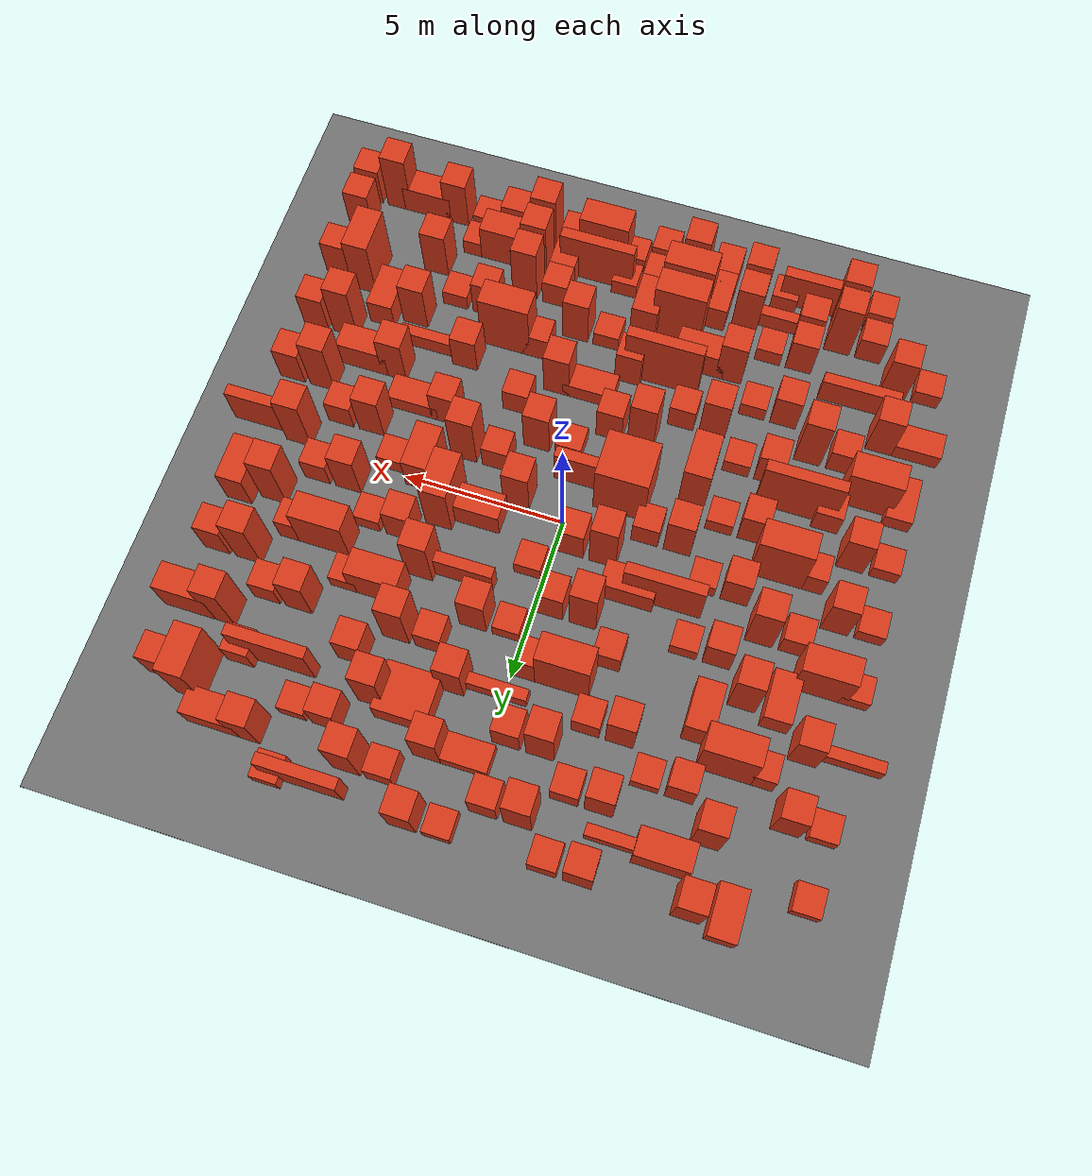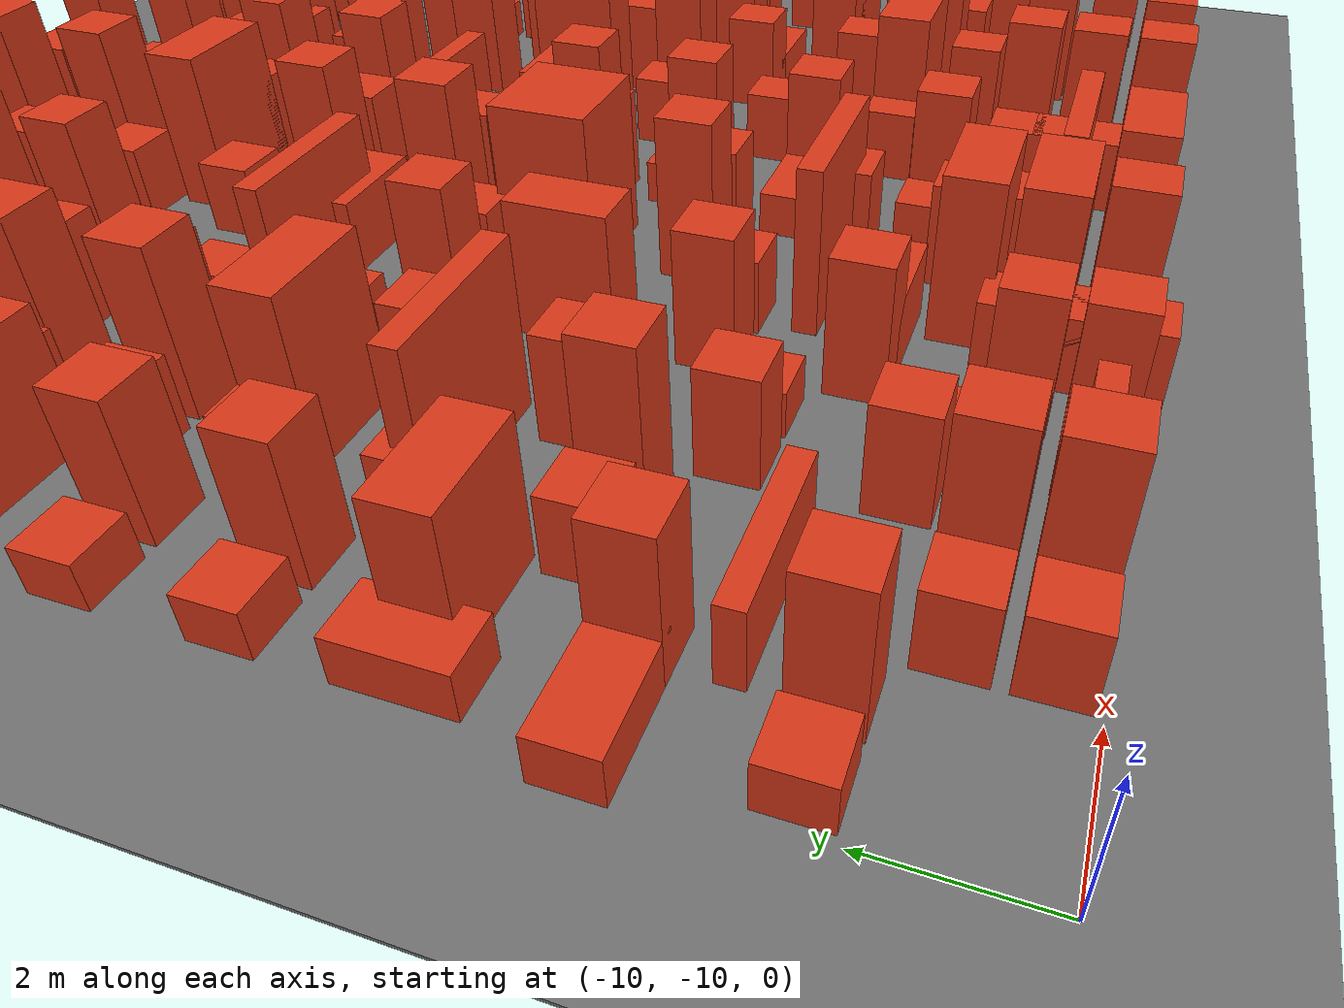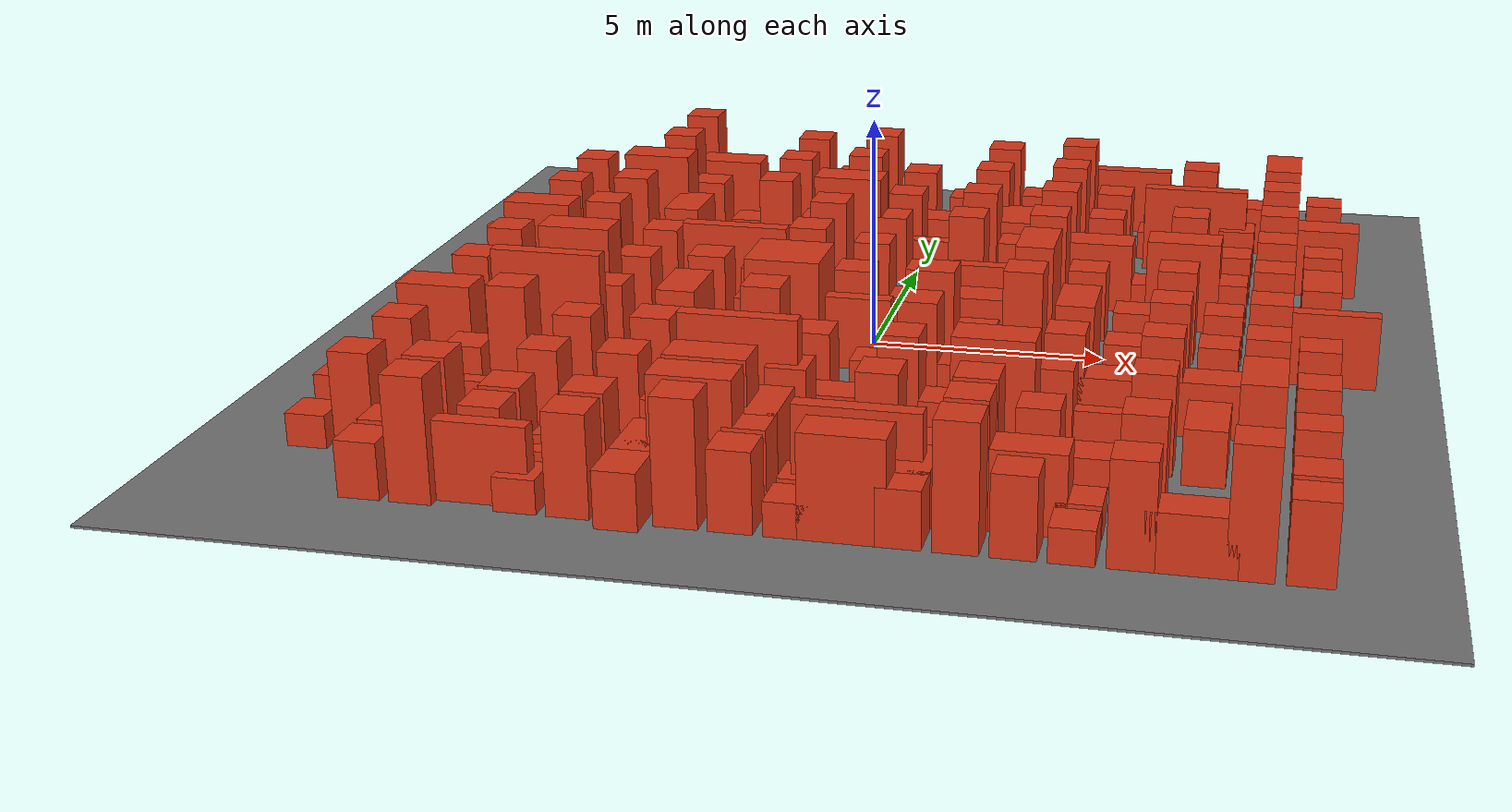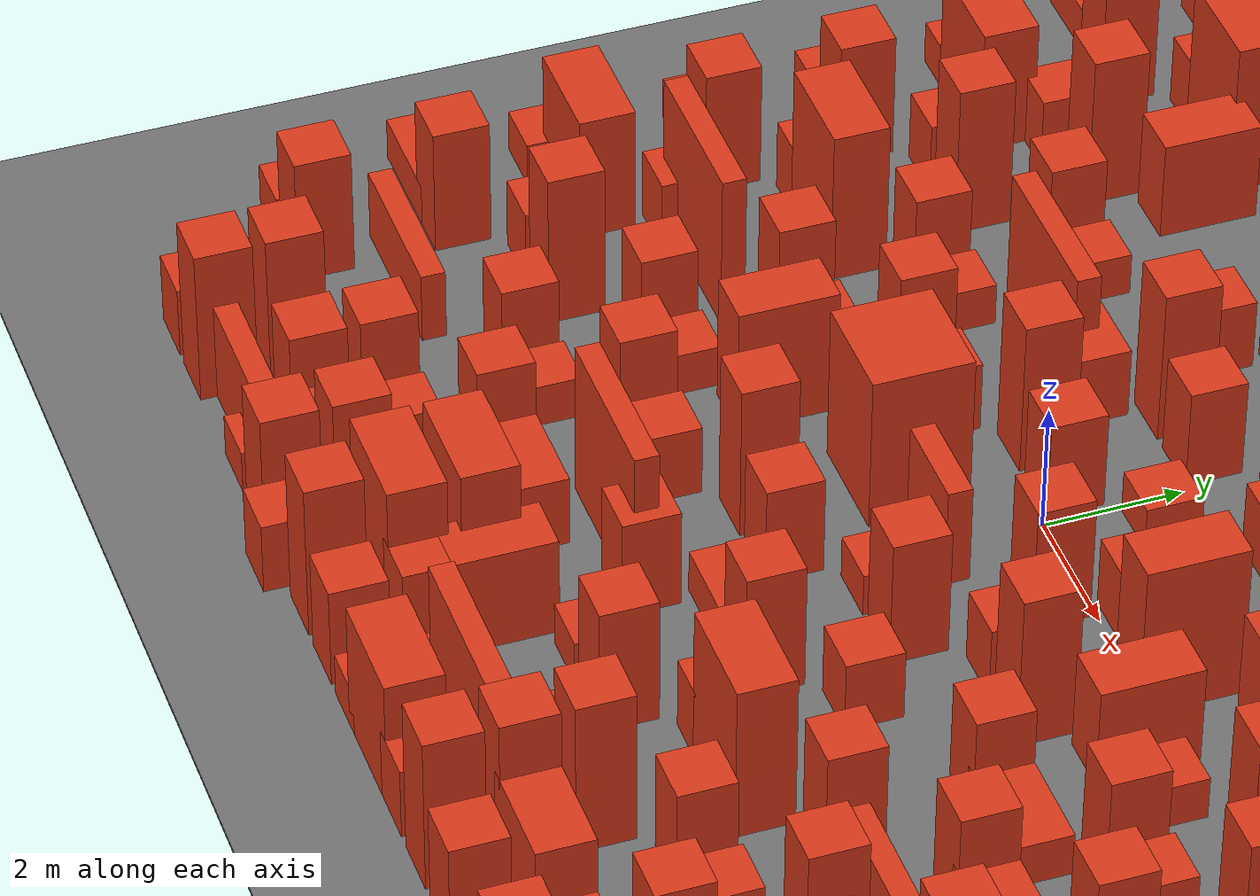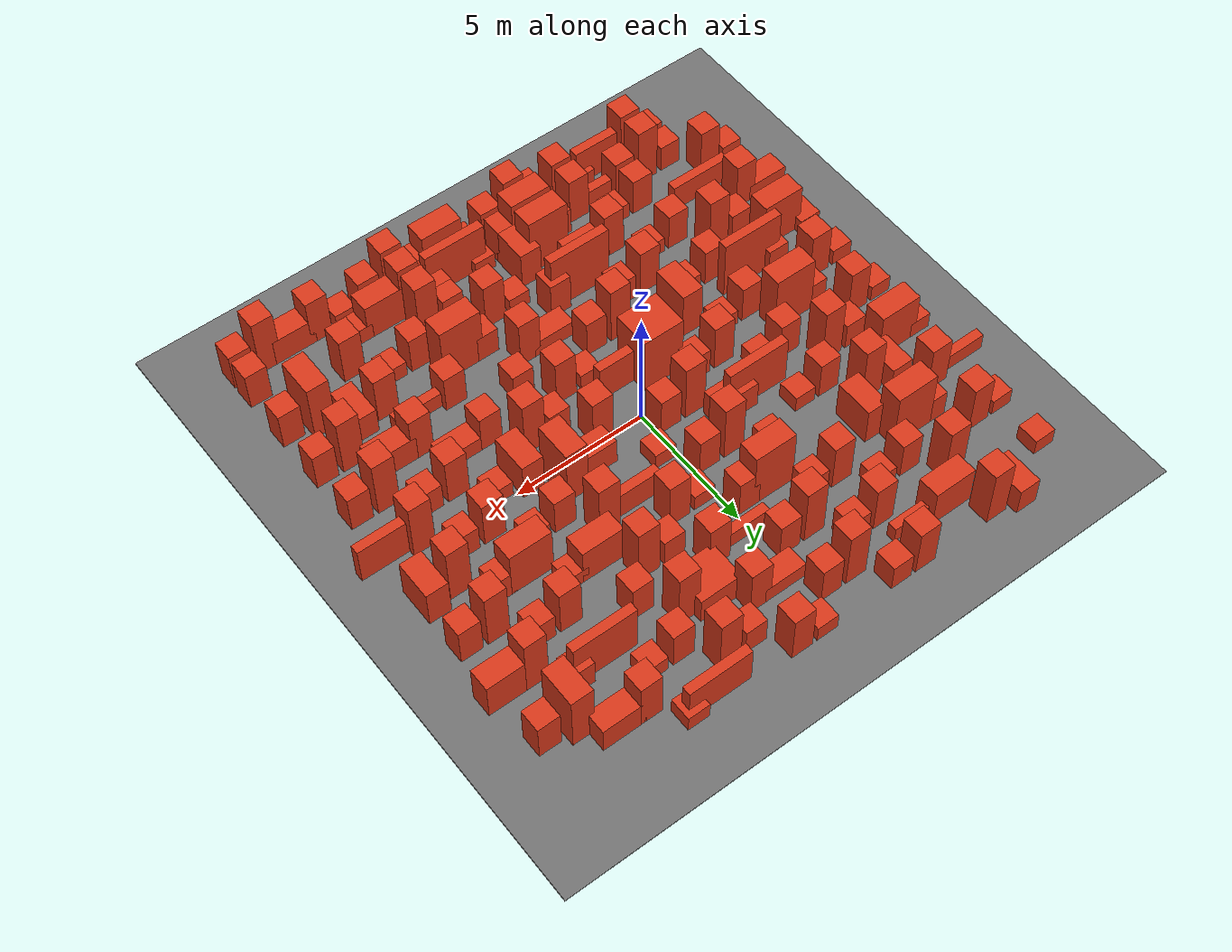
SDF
<?xml version='1.0'?>
<sdf version='1.6'>
  <world name='dense50_ground_footprint'>
    <include><uri>model://sun</uri></include>
    <model name='ground_plane'>
      <static>true</static>
      <link name='link'>
        <collision name='collision'>
          <geometry><box><size>24 24 0.05</size></box></geometry>
        </collision>
        <visual name='visual'>
          <geometry><box><size>24 24 0.05</size></box></geometry>
          <material><ambient>0.35 0.35 0.35 1</ambient><diffuse>0.45 0.45 0.45 1</diffuse></material>
        </visual>
      </link>
    </model>

    <model name='dense50_obstacle_000'>
      <static>true</static>
      <pose>-5.500 -9.500 0.800 0 0 0</pose>
      <link name='link'>
        <collision name='collision'>
          <geometry><box><size>2.400 0.350 1.600</size></box></geometry>
        </collision>
        <visual name='visual'>
          <geometry><box><size>2.400 0.350 1.600</size></box></geometry>
          <material><ambient>0.65 0.16 0.08 1</ambient><diffuse>0.85 0.22 0.10 1</diffuse></material>
        </visual>
      </link>
    </model>

    <model name='dense50_obstacle_001'>
      <static>true</static>
      <pose>-4.500 -9.500 0.350 0 0 0</pose>
      <link name='link'>
        <collision name='collision'>
          <geometry><box><size>0.820 0.820 0.700</size></box></geometry>
        </collision>
        <visual name='visual'>
          <geometry><box><size>0.820 0.820 0.700</size></box></geometry>
          <material><ambient>0.65 0.16 0.08 1</ambient><diffuse>0.85 0.22 0.10 1</diffuse></material>
        </visual>
      </link>
    </model>

    <model name='dense50_obstacle_002'>
      <static>true</static>
      <pose>-1.500 -9.500 1.250 0 0 0</pose>
      <link name='link'>
        <collision name='collision'>
          <geometry><box><size>0.820 0.820 2.500</size></box></geometry>
        </collision>
        <visual name='visual'>
          <geometry><box><size>0.820 0.820 2.500</size></box></geometry>
          <material><ambient>0.65 0.16 0.08 1</ambient><diffuse>0.85 0.22 0.10 1</diffuse></material>
        </visual>
      </link>
    </model>

    <model name='dense50_obstacle_003'>
      <static>true</static>
      <pose>-0.500 -9.500 0.800 0 0 0</pose>
      <link name='link'>
        <collision name='collision'>
          <geometry><box><size>0.820 0.820 1.600</size></box></geometry>
        </collision>
        <visual name='visual'>
          <geometry><box><size>0.820 0.820 1.600</size></box></geometry>
          <material><ambient>0.65 0.16 0.08 1</ambient><diffuse>0.85 0.22 0.10 1</diffuse></material>
        </visual>
      </link>
    </model>

    <model name='dense50_obstacle_004'>
      <static>true</static>
      <pose>2.500 -9.500 0.575 0 0 0</pose>
      <link name='link'>
        <collision name='collision'>
          <geometry><box><size>0.820 0.820 1.150</size></box></geometry>
        </collision>
        <visual name='visual'>
          <geometry><box><size>0.820 0.820 1.150</size></box></geometry>
          <material><ambient>0.65 0.16 0.08 1</ambient><diffuse>0.85 0.22 0.10 1</diffuse></material>
        </visual>
      </link>
    </model>

    <model name='dense50_obstacle_005'>
      <static>true</static>
      <pose>3.500 -9.500 1.250 0 0 0</pose>
      <link name='link'>
        <collision name='collision'>
          <geometry><box><size>0.820 0.820 2.500</size></box></geometry>
        </collision>
        <visual name='visual'>
          <geometry><box><size>0.820 0.820 2.500</size></box></geometry>
          <material><ambient>0.65 0.16 0.08 1</ambient><diffuse>0.85 0.22 0.10 1</diffuse></material>
        </visual>
      </link>
    </model>

    <model name='dense50_obstacle_006'>
      <static>true</static>
      <pose>6.500 -9.500 1.025 0 0 0</pose>
      <link name='link'>
        <collision name='collision'>
          <geometry><box><size>0.820 0.820 2.050</size></box></geometry>
        </collision>
        <visual name='visual'>
          <geometry><box><size>0.820 0.820 2.050</size></box></geometry>
          <material><ambient>0.65 0.16 0.08 1</ambient><diffuse>0.85 0.22 0.10 1</diffuse></material>
        </visual>
      </link>
    </model>

    <model name='dense50_obstacle_007'>
      <static>true</static>
      <pose>7.500 -9.500 0.575 0 0 0</pose>
      <link name='link'>
        <collision name='collision'>
          <geometry><box><size>1.600 0.820 1.150</size></box></geometry>
        </collision>
        <visual name='visual'>
          <geometry><box><size>1.600 0.820 1.150</size></box></geometry>
          <material><ambient>0.65 0.16 0.08 1</ambient><diffuse>0.85 0.22 0.10 1</diffuse></material>
        </visual>
      </link>
    </model>

    <model name='dense50_obstacle_008'>
      <static>true</static>
      <pose>-7.500 -8.500 0.575 0 0 0</pose>
      <link name='link'>
        <collision name='collision'>
          <geometry><box><size>0.820 0.820 1.150</size></box></geometry>
        </collision>
        <visual name='visual'>
          <geometry><box><size>0.820 0.820 1.150</size></box></geometry>
          <material><ambient>0.65 0.16 0.08 1</ambient><diffuse>0.85 0.22 0.10 1</diffuse></material>
        </visual>
      </link>
    </model>

    <model name='dense50_obstacle_009'>
      <static>true</static>
      <pose>-6.500 -8.500 1.250 0 0 0</pose>
      <link name='link'>
        <collision name='collision'>
          <geometry><box><size>0.820 0.820 2.500</size></box></geometry>
        </collision>
        <visual name='visual'>
          <geometry><box><size>0.820 0.820 2.500</size></box></geometry>
          <material><ambient>0.65 0.16 0.08 1</ambient><diffuse>0.85 0.22 0.10 1</diffuse></material>
        </visual>
      </link>
    </model>

    <model name='dense50_obstacle_010'>
      <static>true</static>
      <pose>-3.500 -8.500 1.025 0 0 0</pose>
      <link name='link'>
        <collision name='collision'>
          <geometry><box><size>0.820 0.820 2.050</size></box></geometry>
        </collision>
        <visual name='visual'>
          <geometry><box><size>0.820 0.820 2.050</size></box></geometry>
          <material><ambient>0.65 0.16 0.08 1</ambient><diffuse>0.85 0.22 0.10 1</diffuse></material>
        </visual>
      </link>
    </model>

    <model name='dense50_obstacle_011'>
      <static>true</static>
      <pose>-2.500 -8.500 0.575 0 0 0</pose>
      <link name='link'>
        <collision name='collision'>
          <geometry><box><size>0.820 1.450 1.150</size></box></geometry>
        </collision>
        <visual name='visual'>
          <geometry><box><size>0.820 1.450 1.150</size></box></geometry>
          <material><ambient>0.65 0.16 0.08 1</ambient><diffuse>0.85 0.22 0.10 1</diffuse></material>
        </visual>
      </link>
    </model>

    <model name='dense50_obstacle_012'>
      <static>true</static>
      <pose>0.500 -8.500 0.350 0 0 0</pose>
      <link name='link'>
        <collision name='collision'>
          <geometry><box><size>0.820 0.820 0.700</size></box></geometry>
        </collision>
        <visual name='visual'>
          <geometry><box><size>0.820 0.820 0.700</size></box></geometry>
          <material><ambient>0.65 0.16 0.08 1</ambient><diffuse>0.85 0.22 0.10 1</diffuse></material>
        </visual>
      </link>
    </model>

    <model name='dense50_obstacle_013'>
      <static>true</static>
      <pose>1.500 -8.500 1.025 0 0 0</pose>
      <link name='link'>
        <collision name='collision'>
          <geometry><box><size>2.400 0.350 2.050</size></box></geometry>
        </collision>
        <visual name='visual'>
          <geometry><box><size>2.400 0.350 2.050</size></box></geometry>
          <material><ambient>0.65 0.16 0.08 1</ambient><diffuse>0.85 0.22 0.10 1</diffuse></material>
        </visual>
      </link>
    </model>

    <model name='dense50_obstacle_014'>
      <static>true</static>
      <pose>4.500 -8.500 0.800 0 0 0</pose>
      <link name='link'>
        <collision name='collision'>
          <geometry><box><size>1.600 0.820 1.600</size></box></geometry>
        </collision>
        <visual name='visual'>
          <geometry><box><size>1.600 0.820 1.600</size></box></geometry>
          <material><ambient>0.65 0.16 0.08 1</ambient><diffuse>0.85 0.22 0.10 1</diffuse></material>
        </visual>
      </link>
    </model>

    <model name='dense50_obstacle_015'>
      <static>true</static>
      <pose>5.500 -8.500 0.350 0 0 0</pose>
      <link name='link'>
        <collision name='collision'>
          <geometry><box><size>0.820 0.820 0.700</size></box></geometry>
        </collision>
        <visual name='visual'>
          <geometry><box><size>0.820 0.820 0.700</size></box></geometry>
          <material><ambient>0.65 0.16 0.08 1</ambient><diffuse>0.85 0.22 0.10 1</diffuse></material>
        </visual>
      </link>
    </model>

    <model name='dense50_obstacle_016'>
      <static>true</static>
      <pose>9.500 -8.500 0.800 0 0 0</pose>
      <link name='link'>
        <collision name='collision'>
          <geometry><box><size>0.820 0.820 1.600</size></box></geometry>
        </collision>
        <visual name='visual'>
          <geometry><box><size>0.820 0.820 1.600</size></box></geometry>
          <material><ambient>0.65 0.16 0.08 1</ambient><diffuse>0.85 0.22 0.10 1</diffuse></material>
        </visual>
      </link>
    </model>

    <model name='dense50_obstacle_017'>
      <static>true</static>
      <pose>-9.500 -7.500 0.350 0 0 0</pose>
      <link name='link'>
        <collision name='collision'>
          <geometry><box><size>0.820 0.820 0.700</size></box></geometry>
        </collision>
        <visual name='visual'>
          <geometry><box><size>0.820 0.820 0.700</size></box></geometry>
          <material><ambient>0.65 0.16 0.08 1</ambient><diffuse>0.85 0.22 0.10 1</diffuse></material>
        </visual>
      </link>
    </model>

    <model name='dense50_obstacle_018'>
      <static>true</static>
      <pose>-8.500 -7.500 1.025 0 0 0</pose>
      <link name='link'>
        <collision name='collision'>
          <geometry><box><size>0.820 0.820 2.050</size></box></geometry>
        </collision>
        <visual name='visual'>
          <geometry><box><size>0.820 0.820 2.050</size></box></geometry>
          <material><ambient>0.65 0.16 0.08 1</ambient><diffuse>0.85 0.22 0.10 1</diffuse></material>
        </visual>
      </link>
    </model>

    <model name='dense50_obstacle_019'>
      <static>true</static>
      <pose>-5.500 -7.500 0.800 0 0 0</pose>
      <link name='link'>
        <collision name='collision'>
          <geometry><box><size>0.820 0.820 1.600</size></box></geometry>
        </collision>
        <visual name='visual'>
          <geometry><box><size>0.820 0.820 1.600</size></box></geometry>
          <material><ambient>0.65 0.16 0.08 1</ambient><diffuse>0.85 0.22 0.10 1</diffuse></material>
        </visual>
      </link>
    </model>

    <model name='dense50_obstacle_020'>
      <static>true</static>
      <pose>-4.500 -7.500 0.350 0 0 0</pose>
      <link name='link'>
        <collision name='collision'>
          <geometry><box><size>0.820 0.820 0.700</size></box></geometry>
        </collision>
        <visual name='visual'>
          <geometry><box><size>0.820 0.820 0.700</size></box></geometry>
          <material><ambient>0.65 0.16 0.08 1</ambient><diffuse>0.85 0.22 0.10 1</diffuse></material>
        </visual>
      </link>
    </model>

    <model name='dense50_obstacle_021'>
      <static>true</static>
      <pose>-1.500 -7.500 1.250 0 0 0</pose>
      <link name='link'>
        <collision name='collision'>
          <geometry><box><size>1.600 0.820 2.500</size></box></geometry>
        </collision>
        <visual name='visual'>
          <geometry><box><size>1.600 0.820 2.500</size></box></geometry>
          <material><ambient>0.65 0.16 0.08 1</ambient><diffuse>0.85 0.22 0.10 1</diffuse></material>
        </visual>
      </link>
    </model>

    <model name='dense50_obstacle_022'>
      <static>true</static>
      <pose>-0.500 -7.500 0.800 0 0 0</pose>
      <link name='link'>
        <collision name='collision'>
          <geometry><box><size>0.820 1.450 1.600</size></box></geometry>
        </collision>
        <visual name='visual'>
          <geometry><box><size>0.820 1.450 1.600</size></box></geometry>
          <material><ambient>0.65 0.16 0.08 1</ambient><diffuse>0.85 0.22 0.10 1</diffuse></material>
        </visual>
      </link>
    </model>

    <model name='dense50_obstacle_023'>
      <static>true</static>
      <pose>2.500 -7.500 0.575 0 0 0</pose>
      <link name='link'>
        <collision name='collision'>
          <geometry><box><size>0.820 0.820 1.150</size></box></geometry>
        </collision>
        <visual name='visual'>
          <geometry><box><size>0.820 0.820 1.150</size></box></geometry>
          <material><ambient>0.65 0.16 0.08 1</ambient><diffuse>0.85 0.22 0.10 1</diffuse></material>
        </visual>
      </link>
    </model>

    <model name='dense50_obstacle_024'>
      <static>true</static>
      <pose>3.500 -7.500 1.250 0 0 0</pose>
      <link name='link'>
        <collision name='collision'>
          <geometry><box><size>0.820 0.820 2.500</size></box></geometry>
        </collision>
        <visual name='visual'>
          <geometry><box><size>0.820 0.820 2.500</size></box></geometry>
          <material><ambient>0.65 0.16 0.08 1</ambient><diffuse>0.85 0.22 0.10 1</diffuse></material>
        </visual>
      </link>
    </model>

    <model name='dense50_obstacle_025'>
      <static>true</static>
      <pose>6.500 -7.500 1.025 0 0 0</pose>
      <link name='link'>
        <collision name='collision'>
          <geometry><box><size>0.820 0.820 2.050</size></box></geometry>
        </collision>
        <visual name='visual'>
          <geometry><box><size>0.820 0.820 2.050</size></box></geometry>
          <material><ambient>0.65 0.16 0.08 1</ambient><diffuse>0.85 0.22 0.10 1</diffuse></material>
        </visual>
      </link>
    </model>

    <model name='dense50_obstacle_026'>
      <static>true</static>
      <pose>-7.500 -6.500 0.575 0 0 0</pose>
      <link name='link'>
        <collision name='collision'>
          <geometry><box><size>2.400 0.350 1.150</size></box></geometry>
        </collision>
        <visual name='visual'>
          <geometry><box><size>2.400 0.350 1.150</size></box></geometry>
          <material><ambient>0.65 0.16 0.08 1</ambient><diffuse>0.85 0.22 0.10 1</diffuse></material>
        </visual>
      </link>
    </model>

    <model name='dense50_obstacle_027'>
      <static>true</static>
      <pose>-3.500 -6.500 1.025 0 0 0</pose>
      <link name='link'>
        <collision name='collision'>
          <geometry><box><size>0.820 0.820 2.050</size></box></geometry>
        </collision>
        <visual name='visual'>
          <geometry><box><size>0.820 0.820 2.050</size></box></geometry>
          <material><ambient>0.65 0.16 0.08 1</ambient><diffuse>0.85 0.22 0.10 1</diffuse></material>
        </visual>
      </link>
    </model>

    <model name='dense50_obstacle_028'>
      <static>true</static>
      <pose>-2.500 -6.500 0.575 0 0 0</pose>
      <link name='link'>
        <collision name='collision'>
          <geometry><box><size>1.600 0.820 1.150</size></box></geometry>
        </collision>
        <visual name='visual'>
          <geometry><box><size>1.600 0.820 1.150</size></box></geometry>
          <material><ambient>0.65 0.16 0.08 1</ambient><diffuse>0.85 0.22 0.10 1</diffuse></material>
        </visual>
      </link>
    </model>

    <model name='dense50_obstacle_029'>
      <static>true</static>
      <pose>0.500 -6.500 0.350 0 0 0</pose>
      <link name='link'>
        <collision name='collision'>
          <geometry><box><size>0.820 0.820 0.700</size></box></geometry>
        </collision>
        <visual name='visual'>
          <geometry><box><size>0.820 0.820 0.700</size></box></geometry>
          <material><ambient>0.65 0.16 0.08 1</ambient><diffuse>0.85 0.22 0.10 1</diffuse></material>
        </visual>
      </link>
    </model>

    <model name='dense50_obstacle_030'>
      <static>true</static>
      <pose>1.500 -6.500 1.025 0 0 0</pose>
      <link name='link'>
        <collision name='collision'>
          <geometry><box><size>0.820 0.820 2.050</size></box></geometry>
        </collision>
        <visual name='visual'>
          <geometry><box><size>0.820 0.820 2.050</size></box></geometry>
          <material><ambient>0.65 0.16 0.08 1</ambient><diffuse>0.85 0.22 0.10 1</diffuse></material>
        </visual>
      </link>
    </model>

    <model name='dense50_obstacle_031'>
      <static>true</static>
      <pose>4.500 -6.500 0.800 0 0 0</pose>
      <link name='link'>
        <collision name='collision'>
          <geometry><box><size>0.820 0.820 1.600</size></box></geometry>
        </collision>
        <visual name='visual'>
          <geometry><box><size>0.820 0.820 1.600</size></box></geometry>
          <material><ambient>0.65 0.16 0.08 1</ambient><diffuse>0.85 0.22 0.10 1</diffuse></material>
        </visual>
      </link>
    </model>

    <model name='dense50_obstacle_032'>
      <static>true</static>
      <pose>5.500 -6.500 0.350 0 0 0</pose>
      <link name='link'>
        <collision name='collision'>
          <geometry><box><size>0.820 0.820 0.700</size></box></geometry>
        </collision>
        <visual name='visual'>
          <geometry><box><size>0.820 0.820 0.700</size></box></geometry>
          <material><ambient>0.65 0.16 0.08 1</ambient><diffuse>0.85 0.22 0.10 1</diffuse></material>
        </visual>
      </link>
    </model>

    <model name='dense50_obstacle_033'>
      <static>true</static>
      <pose>8.500 -6.500 1.250 0 0 0</pose>
      <link name='link'>
        <collision name='collision'>
          <geometry><box><size>0.820 1.450 2.500</size></box></geometry>
        </collision>
        <visual name='visual'>
          <geometry><box><size>0.820 1.450 2.500</size></box></geometry>
          <material><ambient>0.65 0.16 0.08 1</ambient><diffuse>0.85 0.22 0.10 1</diffuse></material>
        </visual>
      </link>
    </model>

    <model name='dense50_obstacle_034'>
      <static>true</static>
      <pose>9.500 -6.500 0.800 0 0 0</pose>
      <link name='link'>
        <collision name='collision'>
          <geometry><box><size>0.820 0.820 1.600</size></box></geometry>
        </collision>
        <visual name='visual'>
          <geometry><box><size>0.820 0.820 1.600</size></box></geometry>
          <material><ambient>0.65 0.16 0.08 1</ambient><diffuse>0.85 0.22 0.10 1</diffuse></material>
        </visual>
      </link>
    </model>

    <model name='dense50_obstacle_035'>
      <static>true</static>
      <pose>-9.500 -5.500 0.350 0 0 0</pose>
      <link name='link'>
        <collision name='collision'>
          <geometry><box><size>1.600 0.820 0.700</size></box></geometry>
        </collision>
        <visual name='visual'>
          <geometry><box><size>1.600 0.820 0.700</size></box></geometry>
          <material><ambient>0.65 0.16 0.08 1</ambient><diffuse>0.85 0.22 0.10 1</diffuse></material>
        </visual>
      </link>
    </model>

    <model name='dense50_obstacle_036'>
      <static>true</static>
      <pose>-8.500 -5.500 1.025 0 0 0</pose>
      <link name='link'>
        <collision name='collision'>
          <geometry><box><size>0.820 0.820 2.050</size></box></geometry>
        </collision>
        <visual name='visual'>
          <geometry><box><size>0.820 0.820 2.050</size></box></geometry>
          <material><ambient>0.65 0.16 0.08 1</ambient><diffuse>0.85 0.22 0.10 1</diffuse></material>
        </visual>
      </link>
    </model>

    <model name='dense50_obstacle_037'>
      <static>true</static>
      <pose>-5.500 -5.500 0.800 0 0 0</pose>
      <link name='link'>
        <collision name='collision'>
          <geometry><box><size>0.820 0.820 1.600</size></box></geometry>
        </collision>
        <visual name='visual'>
          <geometry><box><size>0.820 0.820 1.600</size></box></geometry>
          <material><ambient>0.65 0.16 0.08 1</ambient><diffuse>0.85 0.22 0.10 1</diffuse></material>
        </visual>
      </link>
    </model>

    <model name='dense50_obstacle_038'>
      <static>true</static>
      <pose>-4.500 -5.500 0.350 0 0 0</pose>
      <link name='link'>
        <collision name='collision'>
          <geometry><box><size>0.820 0.820 0.700</size></box></geometry>
        </collision>
        <visual name='visual'>
          <geometry><box><size>0.820 0.820 0.700</size></box></geometry>
          <material><ambient>0.65 0.16 0.08 1</ambient><diffuse>0.85 0.22 0.10 1</diffuse></material>
        </visual>
      </link>
    </model>

    <model name='dense50_obstacle_039'>
      <static>true</static>
      <pose>-1.500 -5.500 1.250 0 0 0</pose>
      <link name='link'>
        <collision name='collision'>
          <geometry><box><size>2.400 0.350 2.500</size></box></geometry>
        </collision>
        <visual name='visual'>
          <geometry><box><size>2.400 0.350 2.500</size></box></geometry>
          <material><ambient>0.65 0.16 0.08 1</ambient><diffuse>0.85 0.22 0.10 1</diffuse></material>
        </visual>
      </link>
    </model>

    <model name='dense50_obstacle_040'>
      <static>true</static>
      <pose>-0.500 -5.500 0.800 0 0 0</pose>
      <link name='link'>
        <collision name='collision'>
          <geometry><box><size>0.820 0.820 1.600</size></box></geometry>
        </collision>
        <visual name='visual'>
          <geometry><box><size>0.820 0.820 1.600</size></box></geometry>
          <material><ambient>0.65 0.16 0.08 1</ambient><diffuse>0.85 0.22 0.10 1</diffuse></material>
        </visual>
      </link>
    </model>

    <model name='dense50_obstacle_041'>
      <static>true</static>
      <pose>2.500 -5.500 0.575 0 0 0</pose>
      <link name='link'>
        <collision name='collision'>
          <geometry><box><size>0.820 0.820 1.150</size></box></geometry>
        </collision>
        <visual name='visual'>
          <geometry><box><size>0.820 0.820 1.150</size></box></geometry>
          <material><ambient>0.65 0.16 0.08 1</ambient><diffuse>0.85 0.22 0.10 1</diffuse></material>
        </visual>
      </link>
    </model>

    <model name='dense50_obstacle_042'>
      <static>true</static>
      <pose>3.500 -5.500 1.250 0 0 0</pose>
      <link name='link'>
        <collision name='collision'>
          <geometry><box><size>1.600 0.820 2.500</size></box></geometry>
        </collision>
        <visual name='visual'>
          <geometry><box><size>1.600 0.820 2.500</size></box></geometry>
          <material><ambient>0.65 0.16 0.08 1</ambient><diffuse>0.85 0.22 0.10 1</diffuse></material>
        </visual>
      </link>
    </model>

    <model name='dense50_obstacle_043'>
      <static>true</static>
      <pose>6.500 -5.500 1.025 0 0 0</pose>
      <link name='link'>
        <collision name='collision'>
          <geometry><box><size>0.820 0.820 2.050</size></box></geometry>
        </collision>
        <visual name='visual'>
          <geometry><box><size>0.820 0.820 2.050</size></box></geometry>
          <material><ambient>0.65 0.16 0.08 1</ambient><diffuse>0.85 0.22 0.10 1</diffuse></material>
        </visual>
      </link>
    </model>

    <model name='dense50_obstacle_044'>
      <static>true</static>
      <pose>7.500 -5.500 0.575 0 0 0</pose>
      <link name='link'>
        <collision name='collision'>
          <geometry><box><size>0.820 1.450 1.150</size></box></geometry>
        </collision>
        <visual name='visual'>
          <geometry><box><size>0.820 1.450 1.150</size></box></geometry>
          <material><ambient>0.65 0.16 0.08 1</ambient><diffuse>0.85 0.22 0.10 1</diffuse></material>
        </visual>
      </link>
    </model>

    <model name='dense50_obstacle_045'>
      <static>true</static>
      <pose>-7.500 -4.500 0.575 0 0 0</pose>
      <link name='link'>
        <collision name='collision'>
          <geometry><box><size>0.820 0.820 1.150</size></box></geometry>
        </collision>
        <visual name='visual'>
          <geometry><box><size>0.820 0.820 1.150</size></box></geometry>
          <material><ambient>0.65 0.16 0.08 1</ambient><diffuse>0.85 0.22 0.10 1</diffuse></material>
        </visual>
      </link>
    </model>

    <model name='dense50_obstacle_046'>
      <static>true</static>
      <pose>-6.500 -4.500 1.250 0 0 0</pose>
      <link name='link'>
        <collision name='collision'>
          <geometry><box><size>0.820 0.820 2.500</size></box></geometry>
        </collision>
        <visual name='visual'>
          <geometry><box><size>0.820 0.820 2.500</size></box></geometry>
          <material><ambient>0.65 0.16 0.08 1</ambient><diffuse>0.85 0.22 0.10 1</diffuse></material>
        </visual>
      </link>
    </model>

    <model name='dense50_obstacle_047'>
      <static>true</static>
      <pose>-3.500 -4.500 1.025 0 0 0</pose>
      <link name='link'>
        <collision name='collision'>
          <geometry><box><size>0.820 0.820 2.050</size></box></geometry>
        </collision>
        <visual name='visual'>
          <geometry><box><size>0.820 0.820 2.050</size></box></geometry>
          <material><ambient>0.65 0.16 0.08 1</ambient><diffuse>0.85 0.22 0.10 1</diffuse></material>
        </visual>
      </link>
    </model>

    <model name='dense50_obstacle_048'>
      <static>true</static>
      <pose>-2.500 -4.500 0.575 0 0 0</pose>
      <link name='link'>
        <collision name='collision'>
          <geometry><box><size>0.820 0.820 1.150</size></box></geometry>
        </collision>
        <visual name='visual'>
          <geometry><box><size>0.820 0.820 1.150</size></box></geometry>
          <material><ambient>0.65 0.16 0.08 1</ambient><diffuse>0.85 0.22 0.10 1</diffuse></material>
        </visual>
      </link>
    </model>

    <model name='dense50_obstacle_049'>
      <static>true</static>
      <pose>0.500 -4.500 0.350 0 0 0</pose>
      <link name='link'>
        <collision name='collision'>
          <geometry><box><size>1.600 0.820 0.700</size></box></geometry>
        </collision>
        <visual name='visual'>
          <geometry><box><size>1.600 0.820 0.700</size></box></geometry>
          <material><ambient>0.65 0.16 0.08 1</ambient><diffuse>0.85 0.22 0.10 1</diffuse></material>
        </visual>
      </link>
    </model>

    <model name='dense50_obstacle_050'>
      <static>true</static>
      <pose>1.500 -4.500 1.025 0 0 0</pose>
      <link name='link'>
        <collision name='collision'>
          <geometry><box><size>0.820 0.820 2.050</size></box></geometry>
        </collision>
        <visual name='visual'>
          <geometry><box><size>0.820 0.820 2.050</size></box></geometry>
          <material><ambient>0.65 0.16 0.08 1</ambient><diffuse>0.85 0.22 0.10 1</diffuse></material>
        </visual>
      </link>
    </model>

    <model name='dense50_obstacle_051'>
      <static>true</static>
      <pose>4.500 -4.500 0.800 0 0 0</pose>
      <link name='link'>
        <collision name='collision'>
          <geometry><box><size>0.820 0.820 1.600</size></box></geometry>
        </collision>
        <visual name='visual'>
          <geometry><box><size>0.820 0.820 1.600</size></box></geometry>
          <material><ambient>0.65 0.16 0.08 1</ambient><diffuse>0.85 0.22 0.10 1</diffuse></material>
        </visual>
      </link>
    </model>

    <model name='dense50_obstacle_052'>
      <static>true</static>
      <pose>5.500 -4.500 0.350 0 0 0</pose>
      <link name='link'>
        <collision name='collision'>
          <geometry><box><size>2.400 0.350 0.700</size></box></geometry>
        </collision>
        <visual name='visual'>
          <geometry><box><size>2.400 0.350 0.700</size></box></geometry>
          <material><ambient>0.65 0.16 0.08 1</ambient><diffuse>0.85 0.22 0.10 1</diffuse></material>
        </visual>
      </link>
    </model>

    <model name='dense50_obstacle_053'>
      <static>true</static>
      <pose>8.500 -4.500 1.250 0 0 0</pose>
      <link name='link'>
        <collision name='collision'>
          <geometry><box><size>0.820 0.820 2.500</size></box></geometry>
        </collision>
        <visual name='visual'>
          <geometry><box><size>0.820 0.820 2.500</size></box></geometry>
          <material><ambient>0.65 0.16 0.08 1</ambient><diffuse>0.85 0.22 0.10 1</diffuse></material>
        </visual>
      </link>
    </model>

    <model name='dense50_obstacle_054'>
      <static>true</static>
      <pose>9.500 -4.500 0.800 0 0 0</pose>
      <link name='link'>
        <collision name='collision'>
          <geometry><box><size>0.820 0.820 1.600</size></box></geometry>
        </collision>
        <visual name='visual'>
          <geometry><box><size>0.820 0.820 1.600</size></box></geometry>
          <material><ambient>0.65 0.16 0.08 1</ambient><diffuse>0.85 0.22 0.10 1</diffuse></material>
        </visual>
      </link>
    </model>

    <model name='dense50_obstacle_055'>
      <static>true</static>
      <pose>-9.500 -3.500 0.350 0 0 0</pose>
      <link name='link'>
        <collision name='collision'>
          <geometry><box><size>0.820 1.450 0.700</size></box></geometry>
        </collision>
        <visual name='visual'>
          <geometry><box><size>0.820 1.450 0.700</size></box></geometry>
          <material><ambient>0.65 0.16 0.08 1</ambient><diffuse>0.85 0.22 0.10 1</diffuse></material>
        </visual>
      </link>
    </model>

    <model name='dense50_obstacle_056'>
      <static>true</static>
      <pose>-8.500 -3.500 1.025 0 0 0</pose>
      <link name='link'>
        <collision name='collision'>
          <geometry><box><size>1.600 0.820 2.050</size></box></geometry>
        </collision>
        <visual name='visual'>
          <geometry><box><size>1.600 0.820 2.050</size></box></geometry>
          <material><ambient>0.65 0.16 0.08 1</ambient><diffuse>0.85 0.22 0.10 1</diffuse></material>
        </visual>
      </link>
    </model>

    <model name='dense50_obstacle_057'>
      <static>true</static>
      <pose>-5.500 -3.500 0.800 0 0 0</pose>
      <link name='link'>
        <collision name='collision'>
          <geometry><box><size>0.820 0.820 1.600</size></box></geometry>
        </collision>
        <visual name='visual'>
          <geometry><box><size>0.820 0.820 1.600</size></box></geometry>
          <material><ambient>0.65 0.16 0.08 1</ambient><diffuse>0.85 0.22 0.10 1</diffuse></material>
        </visual>
      </link>
    </model>

    <model name='dense50_obstacle_058'>
      <static>true</static>
      <pose>-4.500 -3.500 0.350 0 0 0</pose>
      <link name='link'>
        <collision name='collision'>
          <geometry><box><size>0.820 0.820 0.700</size></box></geometry>
        </collision>
        <visual name='visual'>
          <geometry><box><size>0.820 0.820 0.700</size></box></geometry>
          <material><ambient>0.65 0.16 0.08 1</ambient><diffuse>0.85 0.22 0.10 1</diffuse></material>
        </visual>
      </link>
    </model>

    <model name='dense50_obstacle_059'>
      <static>true</static>
      <pose>-1.500 -3.500 1.250 0 0 0</pose>
      <link name='link'>
        <collision name='collision'>
          <geometry><box><size>0.820 0.820 2.500</size></box></geometry>
        </collision>
        <visual name='visual'>
          <geometry><box><size>0.820 0.820 2.500</size></box></geometry>
          <material><ambient>0.65 0.16 0.08 1</ambient><diffuse>0.85 0.22 0.10 1</diffuse></material>
        </visual>
      </link>
    </model>

    <model name='dense50_obstacle_060'>
      <static>true</static>
      <pose>-0.500 -3.500 0.800 0 0 0</pose>
      <link name='link'>
        <collision name='collision'>
          <geometry><box><size>0.820 0.820 1.600</size></box></geometry>
        </collision>
        <visual name='visual'>
          <geometry><box><size>0.820 0.820 1.600</size></box></geometry>
          <material><ambient>0.65 0.16 0.08 1</ambient><diffuse>0.85 0.22 0.10 1</diffuse></material>
        </visual>
      </link>
    </model>

    <model name='dense50_obstacle_061'>
      <static>true</static>
      <pose>2.500 -3.500 0.575 0 0 0</pose>
      <link name='link'>
        <collision name='collision'>
          <geometry><box><size>0.820 0.820 1.150</size></box></geometry>
        </collision>
        <visual name='visual'>
          <geometry><box><size>0.820 0.820 1.150</size></box></geometry>
          <material><ambient>0.65 0.16 0.08 1</ambient><diffuse>0.85 0.22 0.10 1</diffuse></material>
        </visual>
      </link>
    </model>

    <model name='dense50_obstacle_062'>
      <static>true</static>
      <pose>6.500 -3.500 1.025 0 0 0</pose>
      <link name='link'>
        <collision name='collision'>
          <geometry><box><size>0.820 0.820 2.050</size></box></geometry>
        </collision>
        <visual name='visual'>
          <geometry><box><size>0.820 0.820 2.050</size></box></geometry>
          <material><ambient>0.65 0.16 0.08 1</ambient><diffuse>0.85 0.22 0.10 1</diffuse></material>
        </visual>
      </link>
    </model>

    <model name='dense50_obstacle_063'>
      <static>true</static>
      <pose>7.500 -3.500 0.575 0 0 0</pose>
      <link name='link'>
        <collision name='collision'>
          <geometry><box><size>1.600 0.820 1.150</size></box></geometry>
        </collision>
        <visual name='visual'>
          <geometry><box><size>1.600 0.820 1.150</size></box></geometry>
          <material><ambient>0.65 0.16 0.08 1</ambient><diffuse>0.85 0.22 0.10 1</diffuse></material>
        </visual>
      </link>
    </model>

    <model name='dense50_obstacle_064'>
      <static>true</static>
      <pose>-7.500 -2.500 0.575 0 0 0</pose>
      <link name='link'>
        <collision name='collision'>
          <geometry><box><size>0.820 0.820 1.150</size></box></geometry>
        </collision>
        <visual name='visual'>
          <geometry><box><size>0.820 0.820 1.150</size></box></geometry>
          <material><ambient>0.65 0.16 0.08 1</ambient><diffuse>0.85 0.22 0.10 1</diffuse></material>
        </visual>
      </link>
    </model>

    <model name='dense50_obstacle_065'>
      <static>true</static>
      <pose>-6.500 -2.500 1.250 0 0 0</pose>
      <link name='link'>
        <collision name='collision'>
          <geometry><box><size>2.400 0.350 2.500</size></box></geometry>
        </collision>
        <visual name='visual'>
          <geometry><box><size>2.400 0.350 2.500</size></box></geometry>
          <material><ambient>0.65 0.16 0.08 1</ambient><diffuse>0.85 0.22 0.10 1</diffuse></material>
        </visual>
      </link>
    </model>

    <model name='dense50_obstacle_066'>
      <static>true</static>
      <pose>-3.500 -2.500 1.025 0 0 0</pose>
      <link name='link'>
        <collision name='collision'>
          <geometry><box><size>0.820 1.450 2.050</size></box></geometry>
        </collision>
        <visual name='visual'>
          <geometry><box><size>0.820 1.450 2.050</size></box></geometry>
          <material><ambient>0.65 0.16 0.08 1</ambient><diffuse>0.85 0.22 0.10 1</diffuse></material>
        </visual>
      </link>
    </model>

    <model name='dense50_obstacle_067'>
      <static>true</static>
      <pose>0.500 -2.500 0.350 0 0 0</pose>
      <link name='link'>
        <collision name='collision'>
          <geometry><box><size>0.820 0.820 0.700</size></box></geometry>
        </collision>
        <visual name='visual'>
          <geometry><box><size>0.820 0.820 0.700</size></box></geometry>
          <material><ambient>0.65 0.16 0.08 1</ambient><diffuse>0.85 0.22 0.10 1</diffuse></material>
        </visual>
      </link>
    </model>

    <model name='dense50_obstacle_068'>
      <static>true</static>
      <pose>1.500 -2.500 1.025 0 0 0</pose>
      <link name='link'>
        <collision name='collision'>
          <geometry><box><size>0.820 0.820 2.050</size></box></geometry>
        </collision>
        <visual name='visual'>
          <geometry><box><size>0.820 0.820 2.050</size></box></geometry>
          <material><ambient>0.65 0.16 0.08 1</ambient><diffuse>0.85 0.22 0.10 1</diffuse></material>
        </visual>
      </link>
    </model>

    <model name='dense50_obstacle_069'>
      <static>true</static>
      <pose>4.500 -2.500 0.800 0 0 0</pose>
      <link name='link'>
        <collision name='collision'>
          <geometry><box><size>0.820 0.820 1.600</size></box></geometry>
        </collision>
        <visual name='visual'>
          <geometry><box><size>0.820 0.820 1.600</size></box></geometry>
          <material><ambient>0.65 0.16 0.08 1</ambient><diffuse>0.85 0.22 0.10 1</diffuse></material>
        </visual>
      </link>
    </model>

    <model name='dense50_obstacle_070'>
      <static>true</static>
      <pose>5.500 -2.500 0.350 0 0 0</pose>
      <link name='link'>
        <collision name='collision'>
          <geometry><box><size>1.600 0.820 0.700</size></box></geometry>
        </collision>
        <visual name='visual'>
          <geometry><box><size>1.600 0.820 0.700</size></box></geometry>
          <material><ambient>0.65 0.16 0.08 1</ambient><diffuse>0.85 0.22 0.10 1</diffuse></material>
        </visual>
      </link>
    </model>

    <model name='dense50_obstacle_071'>
      <static>true</static>
      <pose>8.500 -2.500 1.250 0 0 0</pose>
      <link name='link'>
        <collision name='collision'>
          <geometry><box><size>0.820 0.820 2.500</size></box></geometry>
        </collision>
        <visual name='visual'>
          <geometry><box><size>0.820 0.820 2.500</size></box></geometry>
          <material><ambient>0.65 0.16 0.08 1</ambient><diffuse>0.85 0.22 0.10 1</diffuse></material>
        </visual>
      </link>
    </model>

    <model name='dense50_obstacle_072'>
      <static>true</static>
      <pose>9.500 -2.500 0.800 0 0 0</pose>
      <link name='link'>
        <collision name='collision'>
          <geometry><box><size>0.820 0.820 1.600</size></box></geometry>
        </collision>
        <visual name='visual'>
          <geometry><box><size>0.820 0.820 1.600</size></box></geometry>
          <material><ambient>0.65 0.16 0.08 1</ambient><diffuse>0.85 0.22 0.10 1</diffuse></material>
        </visual>
      </link>
    </model>

    <model name='dense50_obstacle_073'>
      <static>true</static>
      <pose>-9.500 -1.500 0.350 0 0 0</pose>
      <link name='link'>
        <collision name='collision'>
          <geometry><box><size>0.820 0.820 0.700</size></box></geometry>
        </collision>
        <visual name='visual'>
          <geometry><box><size>0.820 0.820 0.700</size></box></geometry>
          <material><ambient>0.65 0.16 0.08 1</ambient><diffuse>0.85 0.22 0.10 1</diffuse></material>
        </visual>
      </link>
    </model>

    <model name='dense50_obstacle_074'>
      <static>true</static>
      <pose>-8.500 -1.500 1.025 0 0 0</pose>
      <link name='link'>
        <collision name='collision'>
          <geometry><box><size>0.820 0.820 2.050</size></box></geometry>
        </collision>
        <visual name='visual'>
          <geometry><box><size>0.820 0.820 2.050</size></box></geometry>
          <material><ambient>0.65 0.16 0.08 1</ambient><diffuse>0.85 0.22 0.10 1</diffuse></material>
        </visual>
      </link>
    </model>

    <model name='dense50_obstacle_075'>
      <static>true</static>
      <pose>-5.500 -1.500 0.800 0 0 0</pose>
      <link name='link'>
        <collision name='collision'>
          <geometry><box><size>0.820 0.820 1.600</size></box></geometry>
        </collision>
        <visual name='visual'>
          <geometry><box><size>0.820 0.820 1.600</size></box></geometry>
          <material><ambient>0.65 0.16 0.08 1</ambient><diffuse>0.85 0.22 0.10 1</diffuse></material>
        </visual>
      </link>
    </model>

    <model name='dense50_obstacle_076'>
      <static>true</static>
      <pose>-4.500 -1.500 0.350 0 0 0</pose>
      <link name='link'>
        <collision name='collision'>
          <geometry><box><size>0.820 0.820 0.700</size></box></geometry>
        </collision>
        <visual name='visual'>
          <geometry><box><size>0.820 0.820 0.700</size></box></geometry>
          <material><ambient>0.65 0.16 0.08 1</ambient><diffuse>0.85 0.22 0.10 1</diffuse></material>
        </visual>
      </link>
    </model>

    <model name='dense50_obstacle_077'>
      <static>true</static>
      <pose>-1.500 -1.500 1.250 0 0 0</pose>
      <link name='link'>
        <collision name='collision'>
          <geometry><box><size>1.600 1.450 2.500</size></box></geometry>
        </collision>
        <visual name='visual'>
          <geometry><box><size>1.600 1.450 2.500</size></box></geometry>
          <material><ambient>0.65 0.16 0.08 1</ambient><diffuse>0.85 0.22 0.10 1</diffuse></material>
        </visual>
      </link>
    </model>

    <model name='dense50_obstacle_078'>
      <static>true</static>
      <pose>-0.500 -1.500 0.800 0 0 0</pose>
      <link name='link'>
        <collision name='collision'>
          <geometry><box><size>2.400 0.350 1.600</size></box></geometry>
        </collision>
        <visual name='visual'>
          <geometry><box><size>2.400 0.350 1.600</size></box></geometry>
          <material><ambient>0.65 0.16 0.08 1</ambient><diffuse>0.85 0.22 0.10 1</diffuse></material>
        </visual>
      </link>
    </model>

    <model name='dense50_obstacle_079'>
      <static>true</static>
      <pose>2.500 -1.500 0.575 0 0 0</pose>
      <link name='link'>
        <collision name='collision'>
          <geometry><box><size>0.820 0.820 1.150</size></box></geometry>
        </collision>
        <visual name='visual'>
          <geometry><box><size>0.820 0.820 1.150</size></box></geometry>
          <material><ambient>0.65 0.16 0.08 1</ambient><diffuse>0.85 0.22 0.10 1</diffuse></material>
        </visual>
      </link>
    </model>

    <model name='dense50_obstacle_080'>
      <static>true</static>
      <pose>3.500 -1.500 1.250 0 0 0</pose>
      <link name='link'>
        <collision name='collision'>
          <geometry><box><size>0.820 0.820 2.500</size></box></geometry>
        </collision>
        <visual name='visual'>
          <geometry><box><size>0.820 0.820 2.500</size></box></geometry>
          <material><ambient>0.65 0.16 0.08 1</ambient><diffuse>0.85 0.22 0.10 1</diffuse></material>
        </visual>
      </link>
    </model>

    <model name='dense50_obstacle_081'>
      <static>true</static>
      <pose>6.500 -1.500 1.025 0 0 0</pose>
      <link name='link'>
        <collision name='collision'>
          <geometry><box><size>0.820 0.820 2.050</size></box></geometry>
        </collision>
        <visual name='visual'>
          <geometry><box><size>0.820 0.820 2.050</size></box></geometry>
          <material><ambient>0.65 0.16 0.08 1</ambient><diffuse>0.85 0.22 0.10 1</diffuse></material>
        </visual>
      </link>
    </model>

    <model name='dense50_obstacle_082'>
      <static>true</static>
      <pose>7.500 -1.500 0.575 0 0 0</pose>
      <link name='link'>
        <collision name='collision'>
          <geometry><box><size>0.820 0.820 1.150</size></box></geometry>
        </collision>
        <visual name='visual'>
          <geometry><box><size>0.820 0.820 1.150</size></box></geometry>
          <material><ambient>0.65 0.16 0.08 1</ambient><diffuse>0.85 0.22 0.10 1</diffuse></material>
        </visual>
      </link>
    </model>

    <model name='dense50_obstacle_083'>
      <static>true</static>
      <pose>-7.500 -0.500 0.575 0 0 0</pose>
      <link name='link'>
        <collision name='collision'>
          <geometry><box><size>0.820 0.820 1.150</size></box></geometry>
        </collision>
        <visual name='visual'>
          <geometry><box><size>0.820 0.820 1.150</size></box></geometry>
          <material><ambient>0.65 0.16 0.08 1</ambient><diffuse>0.85 0.22 0.10 1</diffuse></material>
        </visual>
      </link>
    </model>

    <model name='dense50_obstacle_084'>
      <static>true</static>
      <pose>-6.500 -0.500 1.250 0 0 0</pose>
      <link name='link'>
        <collision name='collision'>
          <geometry><box><size>1.600 0.820 2.500</size></box></geometry>
        </collision>
        <visual name='visual'>
          <geometry><box><size>1.600 0.820 2.500</size></box></geometry>
          <material><ambient>0.65 0.16 0.08 1</ambient><diffuse>0.85 0.22 0.10 1</diffuse></material>
        </visual>
      </link>
    </model>

    <model name='dense50_obstacle_085'>
      <static>true</static>
      <pose>-3.500 -0.500 1.025 0 0 0</pose>
      <link name='link'>
        <collision name='collision'>
          <geometry><box><size>0.820 0.820 2.050</size></box></geometry>
        </collision>
        <visual name='visual'>
          <geometry><box><size>0.820 0.820 2.050</size></box></geometry>
          <material><ambient>0.65 0.16 0.08 1</ambient><diffuse>0.85 0.22 0.10 1</diffuse></material>
        </visual>
      </link>
    </model>

    <model name='dense50_obstacle_086'>
      <static>true</static>
      <pose>-2.500 -0.500 0.575 0 0 0</pose>
      <link name='link'>
        <collision name='collision'>
          <geometry><box><size>0.820 0.820 1.150</size></box></geometry>
        </collision>
        <visual name='visual'>
          <geometry><box><size>0.820 0.820 1.150</size></box></geometry>
          <material><ambient>0.65 0.16 0.08 1</ambient><diffuse>0.85 0.22 0.10 1</diffuse></material>
        </visual>
      </link>
    </model>

    <model name='dense50_obstacle_087'>
      <static>true</static>
      <pose>1.500 -0.500 1.025 0 0 0</pose>
      <link name='link'>
        <collision name='collision'>
          <geometry><box><size>0.820 0.820 2.050</size></box></geometry>
        </collision>
        <visual name='visual'>
          <geometry><box><size>0.820 0.820 2.050</size></box></geometry>
          <material><ambient>0.65 0.16 0.08 1</ambient><diffuse>0.85 0.22 0.10 1</diffuse></material>
        </visual>
      </link>
    </model>

    <model name='dense50_obstacle_088'>
      <static>true</static>
      <pose>4.500 -0.500 0.800 0 0 0</pose>
      <link name='link'>
        <collision name='collision'>
          <geometry><box><size>0.820 1.450 1.600</size></box></geometry>
        </collision>
        <visual name='visual'>
          <geometry><box><size>0.820 1.450 1.600</size></box></geometry>
          <material><ambient>0.65 0.16 0.08 1</ambient><diffuse>0.85 0.22 0.10 1</diffuse></material>
        </visual>
      </link>
    </model>

    <model name='dense50_obstacle_089'>
      <static>true</static>
      <pose>5.500 -0.500 0.350 0 0 0</pose>
      <link name='link'>
        <collision name='collision'>
          <geometry><box><size>0.820 0.820 0.700</size></box></geometry>
        </collision>
        <visual name='visual'>
          <geometry><box><size>0.820 0.820 0.700</size></box></geometry>
          <material><ambient>0.65 0.16 0.08 1</ambient><diffuse>0.85 0.22 0.10 1</diffuse></material>
        </visual>
      </link>
    </model>

    <model name='dense50_obstacle_090'>
      <static>true</static>
      <pose>8.500 -0.500 1.250 0 0 0</pose>
      <link name='link'>
        <collision name='collision'>
          <geometry><box><size>0.820 0.820 2.500</size></box></geometry>
        </collision>
        <visual name='visual'>
          <geometry><box><size>0.820 0.820 2.500</size></box></geometry>
          <material><ambient>0.65 0.16 0.08 1</ambient><diffuse>0.85 0.22 0.10 1</diffuse></material>
        </visual>
      </link>
    </model>

    <model name='dense50_obstacle_091'>
      <static>true</static>
      <pose>9.500 -0.500 0.800 0 0 0</pose>
      <link name='link'>
        <collision name='collision'>
          <geometry><box><size>2.400 0.350 1.600</size></box></geometry>
        </collision>
        <visual name='visual'>
          <geometry><box><size>2.400 0.350 1.600</size></box></geometry>
          <material><ambient>0.65 0.16 0.08 1</ambient><diffuse>0.85 0.22 0.10 1</diffuse></material>
        </visual>
      </link>
    </model>

    <model name='dense50_obstacle_092'>
      <static>true</static>
      <pose>-9.500 0.500 0.350 0 0 0</pose>
      <link name='link'>
        <collision name='collision'>
          <geometry><box><size>0.820 0.820 0.700</size></box></geometry>
        </collision>
        <visual name='visual'>
          <geometry><box><size>0.820 0.820 0.700</size></box></geometry>
          <material><ambient>0.65 0.16 0.08 1</ambient><diffuse>0.85 0.22 0.10 1</diffuse></material>
        </visual>
      </link>
    </model>

    <model name='dense50_obstacle_093'>
      <static>true</static>
      <pose>-8.500 0.500 1.025 0 0 0</pose>
      <link name='link'>
        <collision name='collision'>
          <geometry><box><size>0.820 0.820 2.050</size></box></geometry>
        </collision>
        <visual name='visual'>
          <geometry><box><size>0.820 0.820 2.050</size></box></geometry>
          <material><ambient>0.65 0.16 0.08 1</ambient><diffuse>0.85 0.22 0.10 1</diffuse></material>
        </visual>
      </link>
    </model>

    <model name='dense50_obstacle_094'>
      <static>true</static>
      <pose>-5.500 0.500 0.800 0 0 0</pose>
      <link name='link'>
        <collision name='collision'>
          <geometry><box><size>0.820 0.820 1.600</size></box></geometry>
        </collision>
        <visual name='visual'>
          <geometry><box><size>0.820 0.820 1.600</size></box></geometry>
          <material><ambient>0.65 0.16 0.08 1</ambient><diffuse>0.85 0.22 0.10 1</diffuse></material>
        </visual>
      </link>
    </model>

    <model name='dense50_obstacle_095'>
      <static>true</static>
      <pose>-4.500 0.500 0.350 0 0 0</pose>
      <link name='link'>
        <collision name='collision'>
          <geometry><box><size>0.820 0.820 0.700</size></box></geometry>
        </collision>
        <visual name='visual'>
          <geometry><box><size>0.820 0.820 0.700</size></box></geometry>
          <material><ambient>0.65 0.16 0.08 1</ambient><diffuse>0.85 0.22 0.10 1</diffuse></material>
        </visual>
      </link>
    </model>

    <model name='dense50_obstacle_096'>
      <static>true</static>
      <pose>-1.500 0.500 1.250 0 0 0</pose>
      <link name='link'>
        <collision name='collision'>
          <geometry><box><size>0.820 0.820 2.500</size></box></geometry>
        </collision>
        <visual name='visual'>
          <geometry><box><size>0.820 0.820 2.500</size></box></geometry>
          <material><ambient>0.65 0.16 0.08 1</ambient><diffuse>0.85 0.22 0.10 1</diffuse></material>
        </visual>
      </link>
    </model>

    <model name='dense50_obstacle_097'>
      <static>true</static>
      <pose>-0.500 0.500 0.800 0 0 0</pose>
      <link name='link'>
        <collision name='collision'>
          <geometry><box><size>0.820 0.820 1.600</size></box></geometry>
        </collision>
        <visual name='visual'>
          <geometry><box><size>0.820 0.820 1.600</size></box></geometry>
          <material><ambient>0.65 0.16 0.08 1</ambient><diffuse>0.85 0.22 0.10 1</diffuse></material>
        </visual>
      </link>
    </model>

    <model name='dense50_obstacle_098'>
      <static>true</static>
      <pose>2.500 0.500 0.575 0 0 0</pose>
      <link name='link'>
        <collision name='collision'>
          <geometry><box><size>1.600 0.820 1.150</size></box></geometry>
        </collision>
        <visual name='visual'>
          <geometry><box><size>1.600 0.820 1.150</size></box></geometry>
          <material><ambient>0.65 0.16 0.08 1</ambient><diffuse>0.85 0.22 0.10 1</diffuse></material>
        </visual>
      </link>
    </model>

    <model name='dense50_obstacle_099'>
      <static>true</static>
      <pose>3.500 0.500 1.250 0 0 0</pose>
      <link name='link'>
        <collision name='collision'>
          <geometry><box><size>0.820 1.450 2.500</size></box></geometry>
        </collision>
        <visual name='visual'>
          <geometry><box><size>0.820 1.450 2.500</size></box></geometry>
          <material><ambient>0.65 0.16 0.08 1</ambient><diffuse>0.85 0.22 0.10 1</diffuse></material>
        </visual>
      </link>
    </model>

    <model name='dense50_obstacle_100'>
      <static>true</static>
      <pose>6.500 0.500 1.025 0 0 0</pose>
      <link name='link'>
        <collision name='collision'>
          <geometry><box><size>0.820 0.820 2.050</size></box></geometry>
        </collision>
        <visual name='visual'>
          <geometry><box><size>0.820 0.820 2.050</size></box></geometry>
          <material><ambient>0.65 0.16 0.08 1</ambient><diffuse>0.85 0.22 0.10 1</diffuse></material>
        </visual>
      </link>
    </model>

    <model name='dense50_obstacle_101'>
      <static>true</static>
      <pose>7.500 0.500 0.575 0 0 0</pose>
      <link name='link'>
        <collision name='collision'>
          <geometry><box><size>0.820 0.820 1.150</size></box></geometry>
        </collision>
        <visual name='visual'>
          <geometry><box><size>0.820 0.820 1.150</size></box></geometry>
          <material><ambient>0.65 0.16 0.08 1</ambient><diffuse>0.85 0.22 0.10 1</diffuse></material>
        </visual>
      </link>
    </model>

    <model name='dense50_obstacle_102'>
      <static>true</static>
      <pose>-7.500 1.500 0.575 0 0 0</pose>
      <link name='link'>
        <collision name='collision'>
          <geometry><box><size>0.820 0.820 1.150</size></box></geometry>
        </collision>
        <visual name='visual'>
          <geometry><box><size>0.820 0.820 1.150</size></box></geometry>
          <material><ambient>0.65 0.16 0.08 1</ambient><diffuse>0.85 0.22 0.10 1</diffuse></material>
        </visual>
      </link>
    </model>

    <model name='dense50_obstacle_103'>
      <static>true</static>
      <pose>-6.500 1.500 1.250 0 0 0</pose>
      <link name='link'>
        <collision name='collision'>
          <geometry><box><size>0.820 0.820 2.500</size></box></geometry>
        </collision>
        <visual name='visual'>
          <geometry><box><size>0.820 0.820 2.500</size></box></geometry>
          <material><ambient>0.65 0.16 0.08 1</ambient><diffuse>0.85 0.22 0.10 1</diffuse></material>
        </visual>
      </link>
    </model>

    <model name='dense50_obstacle_104'>
      <static>true</static>
      <pose>-3.500 1.500 1.025 0 0 0</pose>
      <link name='link'>
        <collision name='collision'>
          <geometry><box><size>2.400 0.350 2.050</size></box></geometry>
        </collision>
        <visual name='visual'>
          <geometry><box><size>2.400 0.350 2.050</size></box></geometry>
          <material><ambient>0.65 0.16 0.08 1</ambient><diffuse>0.85 0.22 0.10 1</diffuse></material>
        </visual>
      </link>
    </model>

    <model name='dense50_obstacle_105'>
      <static>true</static>
      <pose>-2.500 1.500 0.575 0 0 0</pose>
      <link name='link'>
        <collision name='collision'>
          <geometry><box><size>1.600 0.820 1.150</size></box></geometry>
        </collision>
        <visual name='visual'>
          <geometry><box><size>1.600 0.820 1.150</size></box></geometry>
          <material><ambient>0.65 0.16 0.08 1</ambient><diffuse>0.85 0.22 0.10 1</diffuse></material>
        </visual>
      </link>
    </model>

    <model name='dense50_obstacle_106'>
      <static>true</static>
      <pose>0.500 1.500 0.350 0 0 0</pose>
      <link name='link'>
        <collision name='collision'>
          <geometry><box><size>0.820 0.820 0.700</size></box></geometry>
        </collision>
        <visual name='visual'>
          <geometry><box><size>0.820 0.820 0.700</size></box></geometry>
          <material><ambient>0.65 0.16 0.08 1</ambient><diffuse>0.85 0.22 0.10 1</diffuse></material>
        </visual>
      </link>
    </model>

    <model name='dense50_obstacle_107'>
      <static>true</static>
      <pose>4.500 1.500 0.800 0 0 0</pose>
      <link name='link'>
        <collision name='collision'>
          <geometry><box><size>0.820 0.820 1.600</size></box></geometry>
        </collision>
        <visual name='visual'>
          <geometry><box><size>0.820 0.820 1.600</size></box></geometry>
          <material><ambient>0.65 0.16 0.08 1</ambient><diffuse>0.85 0.22 0.10 1</diffuse></material>
        </visual>
      </link>
    </model>

    <model name='dense50_obstacle_108'>
      <static>true</static>
      <pose>5.500 1.500 0.350 0 0 0</pose>
      <link name='link'>
        <collision name='collision'>
          <geometry><box><size>0.820 0.820 0.700</size></box></geometry>
        </collision>
        <visual name='visual'>
          <geometry><box><size>0.820 0.820 0.700</size></box></geometry>
          <material><ambient>0.65 0.16 0.08 1</ambient><diffuse>0.85 0.22 0.10 1</diffuse></material>
        </visual>
      </link>
    </model>

    <model name='dense50_obstacle_109'>
      <static>true</static>
      <pose>8.500 1.500 1.250 0 0 0</pose>
      <link name='link'>
        <collision name='collision'>
          <geometry><box><size>0.820 0.820 2.500</size></box></geometry>
        </collision>
        <visual name='visual'>
          <geometry><box><size>0.820 0.820 2.500</size></box></geometry>
          <material><ambient>0.65 0.16 0.08 1</ambient><diffuse>0.85 0.22 0.10 1</diffuse></material>
        </visual>
      </link>
    </model>

    <model name='dense50_obstacle_110'>
      <static>true</static>
      <pose>9.500 1.500 0.800 0 0 0</pose>
      <link name='link'>
        <collision name='collision'>
          <geometry><box><size>0.820 1.450 1.600</size></box></geometry>
        </collision>
        <visual name='visual'>
          <geometry><box><size>0.820 1.450 1.600</size></box></geometry>
          <material><ambient>0.65 0.16 0.08 1</ambient><diffuse>0.85 0.22 0.10 1</diffuse></material>
        </visual>
      </link>
    </model>

    <model name='dense50_obstacle_111'>
      <static>true</static>
      <pose>-9.500 2.500 0.350 0 0 0</pose>
      <link name='link'>
        <collision name='collision'>
          <geometry><box><size>0.820 0.820 0.700</size></box></geometry>
        </collision>
        <visual name='visual'>
          <geometry><box><size>0.820 0.820 0.700</size></box></geometry>
          <material><ambient>0.65 0.16 0.08 1</ambient><diffuse>0.85 0.22 0.10 1</diffuse></material>
        </visual>
      </link>
    </model>

    <model name='dense50_obstacle_112'>
      <static>true</static>
      <pose>-8.500 2.500 1.025 0 0 0</pose>
      <link name='link'>
        <collision name='collision'>
          <geometry><box><size>1.600 0.820 2.050</size></box></geometry>
        </collision>
        <visual name='visual'>
          <geometry><box><size>1.600 0.820 2.050</size></box></geometry>
          <material><ambient>0.65 0.16 0.08 1</ambient><diffuse>0.85 0.22 0.10 1</diffuse></material>
        </visual>
      </link>
    </model>

    <model name='dense50_obstacle_113'>
      <static>true</static>
      <pose>-5.500 2.500 0.800 0 0 0</pose>
      <link name='link'>
        <collision name='collision'>
          <geometry><box><size>0.820 0.820 1.600</size></box></geometry>
        </collision>
        <visual name='visual'>
          <geometry><box><size>0.820 0.820 1.600</size></box></geometry>
          <material><ambient>0.65 0.16 0.08 1</ambient><diffuse>0.85 0.22 0.10 1</diffuse></material>
        </visual>
      </link>
    </model>

    <model name='dense50_obstacle_114'>
      <static>true</static>
      <pose>-4.500 2.500 0.350 0 0 0</pose>
      <link name='link'>
        <collision name='collision'>
          <geometry><box><size>0.820 0.820 0.700</size></box></geometry>
        </collision>
        <visual name='visual'>
          <geometry><box><size>0.820 0.820 0.700</size></box></geometry>
          <material><ambient>0.65 0.16 0.08 1</ambient><diffuse>0.85 0.22 0.10 1</diffuse></material>
        </visual>
      </link>
    </model>

    <model name='dense50_obstacle_115'>
      <static>true</static>
      <pose>-1.500 2.500 1.250 0 0 0</pose>
      <link name='link'>
        <collision name='collision'>
          <geometry><box><size>0.820 0.820 2.500</size></box></geometry>
        </collision>
        <visual name='visual'>
          <geometry><box><size>0.820 0.820 2.500</size></box></geometry>
          <material><ambient>0.65 0.16 0.08 1</ambient><diffuse>0.85 0.22 0.10 1</diffuse></material>
        </visual>
      </link>
    </model>

    <model name='dense50_obstacle_116'>
      <static>true</static>
      <pose>-0.500 2.500 0.800 0 0 0</pose>
      <link name='link'>
        <collision name='collision'>
          <geometry><box><size>0.820 0.820 1.600</size></box></geometry>
        </collision>
        <visual name='visual'>
          <geometry><box><size>0.820 0.820 1.600</size></box></geometry>
          <material><ambient>0.65 0.16 0.08 1</ambient><diffuse>0.85 0.22 0.10 1</diffuse></material>
        </visual>
      </link>
    </model>

    <model name='dense50_obstacle_117'>
      <static>true</static>
      <pose>2.500 2.500 0.575 0 0 0</pose>
      <link name='link'>
        <collision name='collision'>
          <geometry><box><size>2.400 0.350 1.150</size></box></geometry>
        </collision>
        <visual name='visual'>
          <geometry><box><size>2.400 0.350 1.150</size></box></geometry>
          <material><ambient>0.65 0.16 0.08 1</ambient><diffuse>0.85 0.22 0.10 1</diffuse></material>
        </visual>
      </link>
    </model>

    <model name='dense50_obstacle_118'>
      <static>true</static>
      <pose>3.500 2.500 1.250 0 0 0</pose>
      <link name='link'>
        <collision name='collision'>
          <geometry><box><size>0.820 0.820 2.500</size></box></geometry>
        </collision>
        <visual name='visual'>
          <geometry><box><size>0.820 0.820 2.500</size></box></geometry>
          <material><ambient>0.65 0.16 0.08 1</ambient><diffuse>0.85 0.22 0.10 1</diffuse></material>
        </visual>
      </link>
    </model>

    <model name='dense50_obstacle_119'>
      <static>true</static>
      <pose>6.500 2.500 1.025 0 0 0</pose>
      <link name='link'>
        <collision name='collision'>
          <geometry><box><size>1.600 0.820 2.050</size></box></geometry>
        </collision>
        <visual name='visual'>
          <geometry><box><size>1.600 0.820 2.050</size></box></geometry>
          <material><ambient>0.65 0.16 0.08 1</ambient><diffuse>0.85 0.22 0.10 1</diffuse></material>
        </visual>
      </link>
    </model>

    <model name='dense50_obstacle_120'>
      <static>true</static>
      <pose>7.500 2.500 0.575 0 0 0</pose>
      <link name='link'>
        <collision name='collision'>
          <geometry><box><size>0.820 0.820 1.150</size></box></geometry>
        </collision>
        <visual name='visual'>
          <geometry><box><size>0.820 0.820 1.150</size></box></geometry>
          <material><ambient>0.65 0.16 0.08 1</ambient><diffuse>0.85 0.22 0.10 1</diffuse></material>
        </visual>
      </link>
    </model>

    <model name='dense50_obstacle_121'>
      <static>true</static>
      <pose>-7.500 3.500 0.575 0 0 0</pose>
      <link name='link'>
        <collision name='collision'>
          <geometry><box><size>0.820 1.450 1.150</size></box></geometry>
        </collision>
        <visual name='visual'>
          <geometry><box><size>0.820 1.450 1.150</size></box></geometry>
          <material><ambient>0.65 0.16 0.08 1</ambient><diffuse>0.85 0.22 0.10 1</diffuse></material>
        </visual>
      </link>
    </model>

    <model name='dense50_obstacle_122'>
      <static>true</static>
      <pose>-6.500 3.500 1.250 0 0 0</pose>
      <link name='link'>
        <collision name='collision'>
          <geometry><box><size>0.820 0.820 2.500</size></box></geometry>
        </collision>
        <visual name='visual'>
          <geometry><box><size>0.820 0.820 2.500</size></box></geometry>
          <material><ambient>0.65 0.16 0.08 1</ambient><diffuse>0.85 0.22 0.10 1</diffuse></material>
        </visual>
      </link>
    </model>

    <model name='dense50_obstacle_123'>
      <static>true</static>
      <pose>-2.500 3.500 0.575 0 0 0</pose>
      <link name='link'>
        <collision name='collision'>
          <geometry><box><size>0.820 0.820 1.150</size></box></geometry>
        </collision>
        <visual name='visual'>
          <geometry><box><size>0.820 0.820 1.150</size></box></geometry>
          <material><ambient>0.65 0.16 0.08 1</ambient><diffuse>0.85 0.22 0.10 1</diffuse></material>
        </visual>
      </link>
    </model>

    <model name='dense50_obstacle_124'>
      <static>true</static>
      <pose>0.500 3.500 0.350 0 0 0</pose>
      <link name='link'>
        <collision name='collision'>
          <geometry><box><size>0.820 0.820 0.700</size></box></geometry>
        </collision>
        <visual name='visual'>
          <geometry><box><size>0.820 0.820 0.700</size></box></geometry>
          <material><ambient>0.65 0.16 0.08 1</ambient><diffuse>0.85 0.22 0.10 1</diffuse></material>
        </visual>
      </link>
    </model>

    <model name='dense50_obstacle_125'>
      <static>true</static>
      <pose>1.500 3.500 1.025 0 0 0</pose>
      <link name='link'>
        <collision name='collision'>
          <geometry><box><size>0.820 0.820 2.050</size></box></geometry>
        </collision>
        <visual name='visual'>
          <geometry><box><size>0.820 0.820 2.050</size></box></geometry>
          <material><ambient>0.65 0.16 0.08 1</ambient><diffuse>0.85 0.22 0.10 1</diffuse></material>
        </visual>
      </link>
    </model>

    <model name='dense50_obstacle_126'>
      <static>true</static>
      <pose>4.500 3.500 0.800 0 0 0</pose>
      <link name='link'>
        <collision name='collision'>
          <geometry><box><size>1.600 0.820 1.600</size></box></geometry>
        </collision>
        <visual name='visual'>
          <geometry><box><size>1.600 0.820 1.600</size></box></geometry>
          <material><ambient>0.65 0.16 0.08 1</ambient><diffuse>0.85 0.22 0.10 1</diffuse></material>
        </visual>
      </link>
    </model>

    <model name='dense50_obstacle_127'>
      <static>true</static>
      <pose>5.500 3.500 0.350 0 0 0</pose>
      <link name='link'>
        <collision name='collision'>
          <geometry><box><size>0.820 0.820 0.700</size></box></geometry>
        </collision>
        <visual name='visual'>
          <geometry><box><size>0.820 0.820 0.700</size></box></geometry>
          <material><ambient>0.65 0.16 0.08 1</ambient><diffuse>0.85 0.22 0.10 1</diffuse></material>
        </visual>
      </link>
    </model>

    <model name='dense50_obstacle_128'>
      <static>true</static>
      <pose>8.500 3.500 1.250 0 0 0</pose>
      <link name='link'>
        <collision name='collision'>
          <geometry><box><size>0.820 0.820 2.500</size></box></geometry>
        </collision>
        <visual name='visual'>
          <geometry><box><size>0.820 0.820 2.500</size></box></geometry>
          <material><ambient>0.65 0.16 0.08 1</ambient><diffuse>0.85 0.22 0.10 1</diffuse></material>
        </visual>
      </link>
    </model>

    <model name='dense50_obstacle_129'>
      <static>true</static>
      <pose>9.500 3.500 0.800 0 0 0</pose>
      <link name='link'>
        <collision name='collision'>
          <geometry><box><size>0.820 0.820 1.600</size></box></geometry>
        </collision>
        <visual name='visual'>
          <geometry><box><size>0.820 0.820 1.600</size></box></geometry>
          <material><ambient>0.65 0.16 0.08 1</ambient><diffuse>0.85 0.22 0.10 1</diffuse></material>
        </visual>
      </link>
    </model>

    <model name='dense50_obstacle_130'>
      <static>true</static>
      <pose>-9.500 4.500 0.350 0 0 0</pose>
      <link name='link'>
        <collision name='collision'>
          <geometry><box><size>2.400 0.350 0.700</size></box></geometry>
        </collision>
        <visual name='visual'>
          <geometry><box><size>2.400 0.350 0.700</size></box></geometry>
          <material><ambient>0.65 0.16 0.08 1</ambient><diffuse>0.85 0.22 0.10 1</diffuse></material>
        </visual>
      </link>
    </model>

    <model name='dense50_obstacle_131'>
      <static>true</static>
      <pose>-8.500 4.500 1.025 0 0 0</pose>
      <link name='link'>
        <collision name='collision'>
          <geometry><box><size>0.820 0.820 2.050</size></box></geometry>
        </collision>
        <visual name='visual'>
          <geometry><box><size>0.820 0.820 2.050</size></box></geometry>
          <material><ambient>0.65 0.16 0.08 1</ambient><diffuse>0.85 0.22 0.10 1</diffuse></material>
        </visual>
      </link>
    </model>

    <model name='dense50_obstacle_132'>
      <static>true</static>
      <pose>-5.500 4.500 0.800 0 0 0</pose>
      <link name='link'>
        <collision name='collision'>
          <geometry><box><size>0.820 1.450 1.600</size></box></geometry>
        </collision>
        <visual name='visual'>
          <geometry><box><size>0.820 1.450 1.600</size></box></geometry>
          <material><ambient>0.65 0.16 0.08 1</ambient><diffuse>0.85 0.22 0.10 1</diffuse></material>
        </visual>
      </link>
    </model>

    <model name='dense50_obstacle_133'>
      <static>true</static>
      <pose>-1.500 4.500 1.250 0 0 0</pose>
      <link name='link'>
        <collision name='collision'>
          <geometry><box><size>1.600 0.820 2.500</size></box></geometry>
        </collision>
        <visual name='visual'>
          <geometry><box><size>1.600 0.820 2.500</size></box></geometry>
          <material><ambient>0.65 0.16 0.08 1</ambient><diffuse>0.85 0.22 0.10 1</diffuse></material>
        </visual>
      </link>
    </model>

    <model name='dense50_obstacle_134'>
      <static>true</static>
      <pose>-0.500 4.500 0.800 0 0 0</pose>
      <link name='link'>
        <collision name='collision'>
          <geometry><box><size>0.820 0.820 1.600</size></box></geometry>
        </collision>
        <visual name='visual'>
          <geometry><box><size>0.820 0.820 1.600</size></box></geometry>
          <material><ambient>0.65 0.16 0.08 1</ambient><diffuse>0.85 0.22 0.10 1</diffuse></material>
        </visual>
      </link>
    </model>

    <model name='dense50_obstacle_135'>
      <static>true</static>
      <pose>2.500 4.500 0.575 0 0 0</pose>
      <link name='link'>
        <collision name='collision'>
          <geometry><box><size>0.820 0.820 1.150</size></box></geometry>
        </collision>
        <visual name='visual'>
          <geometry><box><size>0.820 0.820 1.150</size></box></geometry>
          <material><ambient>0.65 0.16 0.08 1</ambient><diffuse>0.85 0.22 0.10 1</diffuse></material>
        </visual>
      </link>
    </model>

    <model name='dense50_obstacle_136'>
      <static>true</static>
      <pose>3.500 4.500 1.250 0 0 0</pose>
      <link name='link'>
        <collision name='collision'>
          <geometry><box><size>0.820 0.820 2.500</size></box></geometry>
        </collision>
        <visual name='visual'>
          <geometry><box><size>0.820 0.820 2.500</size></box></geometry>
          <material><ambient>0.65 0.16 0.08 1</ambient><diffuse>0.85 0.22 0.10 1</diffuse></material>
        </visual>
      </link>
    </model>

    <model name='dense50_obstacle_137'>
      <static>true</static>
      <pose>6.500 4.500 1.025 0 0 0</pose>
      <link name='link'>
        <collision name='collision'>
          <geometry><box><size>0.820 0.820 2.050</size></box></geometry>
        </collision>
        <visual name='visual'>
          <geometry><box><size>0.820 0.820 2.050</size></box></geometry>
          <material><ambient>0.65 0.16 0.08 1</ambient><diffuse>0.85 0.22 0.10 1</diffuse></material>
        </visual>
      </link>
    </model>

    <model name='dense50_obstacle_138'>
      <static>true</static>
      <pose>7.500 4.500 0.575 0 0 0</pose>
      <link name='link'>
        <collision name='collision'>
          <geometry><box><size>0.820 0.820 1.150</size></box></geometry>
        </collision>
        <visual name='visual'>
          <geometry><box><size>0.820 0.820 1.150</size></box></geometry>
          <material><ambient>0.65 0.16 0.08 1</ambient><diffuse>0.85 0.22 0.10 1</diffuse></material>
        </visual>
      </link>
    </model>

    <model name='dense50_obstacle_139'>
      <static>true</static>
      <pose>-7.500 5.500 0.575 0 0 0</pose>
      <link name='link'>
        <collision name='collision'>
          <geometry><box><size>0.820 0.820 1.150</size></box></geometry>
        </collision>
        <visual name='visual'>
          <geometry><box><size>0.820 0.820 1.150</size></box></geometry>
          <material><ambient>0.65 0.16 0.08 1</ambient><diffuse>0.85 0.22 0.10 1</diffuse></material>
        </visual>
      </link>
    </model>

    <model name='dense50_obstacle_140'>
      <static>true</static>
      <pose>-6.500 5.500 1.250 0 0 0</pose>
      <link name='link'>
        <collision name='collision'>
          <geometry><box><size>1.600 0.820 2.500</size></box></geometry>
        </collision>
        <visual name='visual'>
          <geometry><box><size>1.600 0.820 2.500</size></box></geometry>
          <material><ambient>0.65 0.16 0.08 1</ambient><diffuse>0.85 0.22 0.10 1</diffuse></material>
        </visual>
      </link>
    </model>

    <model name='dense50_obstacle_141'>
      <static>true</static>
      <pose>-3.500 5.500 1.025 0 0 0</pose>
      <link name='link'>
        <collision name='collision'>
          <geometry><box><size>0.820 0.820 2.050</size></box></geometry>
        </collision>
        <visual name='visual'>
          <geometry><box><size>0.820 0.820 2.050</size></box></geometry>
          <material><ambient>0.65 0.16 0.08 1</ambient><diffuse>0.85 0.22 0.10 1</diffuse></material>
        </visual>
      </link>
    </model>

    <model name='dense50_obstacle_142'>
      <static>true</static>
      <pose>-2.500 5.500 0.575 0 0 0</pose>
      <link name='link'>
        <collision name='collision'>
          <geometry><box><size>0.820 0.820 1.150</size></box></geometry>
        </collision>
        <visual name='visual'>
          <geometry><box><size>0.820 0.820 1.150</size></box></geometry>
          <material><ambient>0.65 0.16 0.08 1</ambient><diffuse>0.85 0.22 0.10 1</diffuse></material>
        </visual>
      </link>
    </model>

    <model name='dense50_obstacle_143'>
      <static>true</static>
      <pose>0.500 5.500 0.350 0 0 0</pose>
      <link name='link'>
        <collision name='collision'>
          <geometry><box><size>2.400 0.350 0.700</size></box></geometry>
        </collision>
        <visual name='visual'>
          <geometry><box><size>2.400 0.350 0.700</size></box></geometry>
          <material><ambient>0.65 0.16 0.08 1</ambient><diffuse>0.85 0.22 0.10 1</diffuse></material>
        </visual>
      </link>
    </model>

    <model name='dense50_obstacle_144'>
      <static>true</static>
      <pose>1.500 5.500 1.025 0 0 0</pose>
      <link name='link'>
        <collision name='collision'>
          <geometry><box><size>0.820 0.820 2.050</size></box></geometry>
        </collision>
        <visual name='visual'>
          <geometry><box><size>0.820 0.820 2.050</size></box></geometry>
          <material><ambient>0.65 0.16 0.08 1</ambient><diffuse>0.85 0.22 0.10 1</diffuse></material>
        </visual>
      </link>
    </model>

    <model name='dense50_obstacle_145'>
      <static>true</static>
      <pose>4.500 5.500 0.800 0 0 0</pose>
      <link name='link'>
        <collision name='collision'>
          <geometry><box><size>0.820 0.820 1.600</size></box></geometry>
        </collision>
        <visual name='visual'>
          <geometry><box><size>0.820 0.820 1.600</size></box></geometry>
          <material><ambient>0.65 0.16 0.08 1</ambient><diffuse>0.85 0.22 0.10 1</diffuse></material>
        </visual>
      </link>
    </model>

    <model name='dense50_obstacle_146'>
      <static>true</static>
      <pose>8.500 5.500 1.250 0 0 0</pose>
      <link name='link'>
        <collision name='collision'>
          <geometry><box><size>0.820 0.820 2.500</size></box></geometry>
        </collision>
        <visual name='visual'>
          <geometry><box><size>0.820 0.820 2.500</size></box></geometry>
          <material><ambient>0.65 0.16 0.08 1</ambient><diffuse>0.85 0.22 0.10 1</diffuse></material>
        </visual>
      </link>
    </model>

    <model name='dense50_obstacle_147'>
      <static>true</static>
      <pose>9.500 5.500 0.800 0 0 0</pose>
      <link name='link'>
        <collision name='collision'>
          <geometry><box><size>1.600 0.820 1.600</size></box></geometry>
        </collision>
        <visual name='visual'>
          <geometry><box><size>1.600 0.820 1.600</size></box></geometry>
          <material><ambient>0.65 0.16 0.08 1</ambient><diffuse>0.85 0.22 0.10 1</diffuse></material>
        </visual>
      </link>
    </model>

    <model name='dense50_obstacle_148'>
      <static>true</static>
      <pose>-9.500 6.500 0.350 0 0 0</pose>
      <link name='link'>
        <collision name='collision'>
          <geometry><box><size>0.820 0.820 0.700</size></box></geometry>
        </collision>
        <visual name='visual'>
          <geometry><box><size>0.820 0.820 0.700</size></box></geometry>
          <material><ambient>0.65 0.16 0.08 1</ambient><diffuse>0.85 0.22 0.10 1</diffuse></material>
        </visual>
      </link>
    </model>

    <model name='dense50_obstacle_149'>
      <static>true</static>
      <pose>-8.500 6.500 1.025 0 0 0</pose>
      <link name='link'>
        <collision name='collision'>
          <geometry><box><size>0.820 0.820 2.050</size></box></geometry>
        </collision>
        <visual name='visual'>
          <geometry><box><size>0.820 0.820 2.050</size></box></geometry>
          <material><ambient>0.65 0.16 0.08 1</ambient><diffuse>0.85 0.22 0.10 1</diffuse></material>
        </visual>
      </link>
    </model>

    <model name='dense50_obstacle_150'>
      <static>true</static>
      <pose>-5.500 6.500 0.800 0 0 0</pose>
      <link name='link'>
        <collision name='collision'>
          <geometry><box><size>0.820 0.820 1.600</size></box></geometry>
        </collision>
        <visual name='visual'>
          <geometry><box><size>0.820 0.820 1.600</size></box></geometry>
          <material><ambient>0.65 0.16 0.08 1</ambient><diffuse>0.85 0.22 0.10 1</diffuse></material>
        </visual>
      </link>
    </model>

    <model name='dense50_obstacle_151'>
      <static>true</static>
      <pose>-4.500 6.500 0.350 0 0 0</pose>
      <link name='link'>
        <collision name='collision'>
          <geometry><box><size>0.820 0.820 0.700</size></box></geometry>
        </collision>
        <visual name='visual'>
          <geometry><box><size>0.820 0.820 0.700</size></box></geometry>
          <material><ambient>0.65 0.16 0.08 1</ambient><diffuse>0.85 0.22 0.10 1</diffuse></material>
        </visual>
      </link>
    </model>

    <model name='dense50_obstacle_152'>
      <static>true</static>
      <pose>-1.500 6.500 1.250 0 0 0</pose>
      <link name='link'>
        <collision name='collision'>
          <geometry><box><size>0.820 0.820 2.500</size></box></geometry>
        </collision>
        <visual name='visual'>
          <geometry><box><size>0.820 0.820 2.500</size></box></geometry>
          <material><ambient>0.65 0.16 0.08 1</ambient><diffuse>0.85 0.22 0.10 1</diffuse></material>
        </visual>
      </link>
    </model>

    <model name='dense50_obstacle_153'>
      <static>true</static>
      <pose>-0.500 6.500 0.800 0 0 0</pose>
      <link name='link'>
        <collision name='collision'>
          <geometry><box><size>0.820 0.820 1.600</size></box></geometry>
        </collision>
        <visual name='visual'>
          <geometry><box><size>0.820 0.820 1.600</size></box></geometry>
          <material><ambient>0.65 0.16 0.08 1</ambient><diffuse>0.85 0.22 0.10 1</diffuse></material>
        </visual>
      </link>
    </model>

    <model name='dense50_obstacle_154'>
      <static>true</static>
      <pose>2.500 6.500 0.575 0 0 0</pose>
      <link name='link'>
        <collision name='collision'>
          <geometry><box><size>1.600 1.450 1.150</size></box></geometry>
        </collision>
        <visual name='visual'>
          <geometry><box><size>1.600 1.450 1.150</size></box></geometry>
          <material><ambient>0.65 0.16 0.08 1</ambient><diffuse>0.85 0.22 0.10 1</diffuse></material>
        </visual>
      </link>
    </model>

    <model name='dense50_obstacle_155'>
      <static>true</static>
      <pose>3.500 6.500 1.250 0 0 0</pose>
      <link name='link'>
        <collision name='collision'>
          <geometry><box><size>0.820 0.820 2.500</size></box></geometry>
        </collision>
        <visual name='visual'>
          <geometry><box><size>0.820 0.820 2.500</size></box></geometry>
          <material><ambient>0.65 0.16 0.08 1</ambient><diffuse>0.85 0.22 0.10 1</diffuse></material>
        </visual>
      </link>
    </model>

    <model name='dense50_obstacle_156'>
      <static>true</static>
      <pose>6.500 6.500 1.025 0 0 0</pose>
      <link name='link'>
        <collision name='collision'>
          <geometry><box><size>2.400 0.350 2.050</size></box></geometry>
        </collision>
        <visual name='visual'>
          <geometry><box><size>2.400 0.350 2.050</size></box></geometry>
          <material><ambient>0.65 0.16 0.08 1</ambient><diffuse>0.85 0.22 0.10 1</diffuse></material>
        </visual>
      </link>
    </model>

    <model name='dense50_obstacle_157'>
      <static>true</static>
      <pose>7.500 6.500 0.575 0 0 0</pose>
      <link name='link'>
        <collision name='collision'>
          <geometry><box><size>0.820 0.820 1.150</size></box></geometry>
        </collision>
        <visual name='visual'>
          <geometry><box><size>0.820 0.820 1.150</size></box></geometry>
          <material><ambient>0.65 0.16 0.08 1</ambient><diffuse>0.85 0.22 0.10 1</diffuse></material>
        </visual>
      </link>
    </model>

    <model name='dense50_obstacle_158'>
      <static>true</static>
      <pose>-6.500 7.500 1.250 0 0 0</pose>
      <link name='link'>
        <collision name='collision'>
          <geometry><box><size>0.820 0.820 2.500</size></box></geometry>
        </collision>
        <visual name='visual'>
          <geometry><box><size>0.820 0.820 2.500</size></box></geometry>
          <material><ambient>0.65 0.16 0.08 1</ambient><diffuse>0.85 0.22 0.10 1</diffuse></material>
        </visual>
      </link>
    </model>

    <model name='dense50_obstacle_159'>
      <static>true</static>
      <pose>-3.500 7.500 1.025 0 0 0</pose>
      <link name='link'>
        <collision name='collision'>
          <geometry><box><size>0.820 0.820 2.050</size></box></geometry>
        </collision>
        <visual name='visual'>
          <geometry><box><size>0.820 0.820 2.050</size></box></geometry>
          <material><ambient>0.65 0.16 0.08 1</ambient><diffuse>0.85 0.22 0.10 1</diffuse></material>
        </visual>
      </link>
    </model>

    <model name='dense50_obstacle_160'>
      <static>true</static>
      <pose>-2.500 7.500 0.575 0 0 0</pose>
      <link name='link'>
        <collision name='collision'>
          <geometry><box><size>0.820 0.820 1.150</size></box></geometry>
        </collision>
        <visual name='visual'>
          <geometry><box><size>0.820 0.820 1.150</size></box></geometry>
          <material><ambient>0.65 0.16 0.08 1</ambient><diffuse>0.85 0.22 0.10 1</diffuse></material>
        </visual>
      </link>
    </model>

    <model name='dense50_obstacle_161'>
      <static>true</static>
      <pose>0.500 7.500 0.350 0 0 0</pose>
      <link name='link'>
        <collision name='collision'>
          <geometry><box><size>1.600 0.820 0.700</size></box></geometry>
        </collision>
        <visual name='visual'>
          <geometry><box><size>1.600 0.820 0.700</size></box></geometry>
          <material><ambient>0.65 0.16 0.08 1</ambient><diffuse>0.85 0.22 0.10 1</diffuse></material>
        </visual>
      </link>
    </model>

    <model name='dense50_obstacle_162'>
      <static>true</static>
      <pose>1.500 7.500 1.025 0 0 0</pose>
      <link name='link'>
        <collision name='collision'>
          <geometry><box><size>0.820 0.820 2.050</size></box></geometry>
        </collision>
        <visual name='visual'>
          <geometry><box><size>0.820 0.820 2.050</size></box></geometry>
          <material><ambient>0.65 0.16 0.08 1</ambient><diffuse>0.85 0.22 0.10 1</diffuse></material>
        </visual>
      </link>
    </model>

    <model name='dense50_obstacle_163'>
      <static>true</static>
      <pose>4.500 7.500 0.800 0 0 0</pose>
      <link name='link'>
        <collision name='collision'>
          <geometry><box><size>0.820 0.820 1.600</size></box></geometry>
        </collision>
        <visual name='visual'>
          <geometry><box><size>0.820 0.820 1.600</size></box></geometry>
          <material><ambient>0.65 0.16 0.08 1</ambient><diffuse>0.85 0.22 0.10 1</diffuse></material>
        </visual>
      </link>
    </model>

    <model name='dense50_obstacle_164'>
      <static>true</static>
      <pose>5.500 7.500 0.350 0 0 0</pose>
      <link name='link'>
        <collision name='collision'>
          <geometry><box><size>0.820 0.820 0.700</size></box></geometry>
        </collision>
        <visual name='visual'>
          <geometry><box><size>0.820 0.820 0.700</size></box></geometry>
          <material><ambient>0.65 0.16 0.08 1</ambient><diffuse>0.85 0.22 0.10 1</diffuse></material>
        </visual>
      </link>
    </model>

    <model name='dense50_obstacle_165'>
      <static>true</static>
      <pose>8.500 7.500 1.250 0 0 0</pose>
      <link name='link'>
        <collision name='collision'>
          <geometry><box><size>0.820 1.450 2.500</size></box></geometry>
        </collision>
        <visual name='visual'>
          <geometry><box><size>0.820 1.450 2.500</size></box></geometry>
          <material><ambient>0.65 0.16 0.08 1</ambient><diffuse>0.85 0.22 0.10 1</diffuse></material>
        </visual>
      </link>
    </model>

    <model name='dense50_obstacle_166'>
      <static>true</static>
      <pose>9.500 7.500 0.800 0 0 0</pose>
      <link name='link'>
        <collision name='collision'>
          <geometry><box><size>0.820 0.820 1.600</size></box></geometry>
        </collision>
        <visual name='visual'>
          <geometry><box><size>0.820 0.820 1.600</size></box></geometry>
          <material><ambient>0.65 0.16 0.08 1</ambient><diffuse>0.85 0.22 0.10 1</diffuse></material>
        </visual>
      </link>
    </model>

    <model name='dense50_obstacle_167'>
      <static>true</static>
      <pose>-9.500 8.500 0.350 0 0 0</pose>
      <link name='link'>
        <collision name='collision'>
          <geometry><box><size>0.820 0.820 0.700</size></box></geometry>
        </collision>
        <visual name='visual'>
          <geometry><box><size>0.820 0.820 0.700</size></box></geometry>
          <material><ambient>0.65 0.16 0.08 1</ambient><diffuse>0.85 0.22 0.10 1</diffuse></material>
        </visual>
      </link>
    </model>

    <model name='dense50_obstacle_168'>
      <static>true</static>
      <pose>-5.500 8.500 0.800 0 0 0</pose>
      <link name='link'>
        <collision name='collision'>
          <geometry><box><size>1.600 0.820 1.600</size></box></geometry>
        </collision>
        <visual name='visual'>
          <geometry><box><size>1.600 0.820 1.600</size></box></geometry>
          <material><ambient>0.65 0.16 0.08 1</ambient><diffuse>0.85 0.22 0.10 1</diffuse></material>
        </visual>
      </link>
    </model>

    <model name='dense50_obstacle_169'>
      <static>true</static>
      <pose>-4.500 8.500 0.350 0 0 0</pose>
      <link name='link'>
        <collision name='collision'>
          <geometry><box><size>2.400 0.350 0.700</size></box></geometry>
        </collision>
        <visual name='visual'>
          <geometry><box><size>2.400 0.350 0.700</size></box></geometry>
          <material><ambient>0.65 0.16 0.08 1</ambient><diffuse>0.85 0.22 0.10 1</diffuse></material>
        </visual>
      </link>
    </model>

    <model name='dense50_obstacle_170'>
      <static>true</static>
      <pose>-1.500 8.500 1.250 0 0 0</pose>
      <link name='link'>
        <collision name='collision'>
          <geometry><box><size>0.820 0.820 2.500</size></box></geometry>
        </collision>
        <visual name='visual'>
          <geometry><box><size>0.820 0.820 2.500</size></box></geometry>
          <material><ambient>0.65 0.16 0.08 1</ambient><diffuse>0.85 0.22 0.10 1</diffuse></material>
        </visual>
      </link>
    </model>

    <model name='dense50_obstacle_171'>
      <static>true</static>
      <pose>-0.500 8.500 0.800 0 0 0</pose>
      <link name='link'>
        <collision name='collision'>
          <geometry><box><size>0.820 0.820 1.600</size></box></geometry>
        </collision>
        <visual name='visual'>
          <geometry><box><size>0.820 0.820 1.600</size></box></geometry>
          <material><ambient>0.65 0.16 0.08 1</ambient><diffuse>0.85 0.22 0.10 1</diffuse></material>
        </visual>
      </link>
    </model>

    <model name='dense50_obstacle_172'>
      <static>true</static>
      <pose>2.500 8.500 0.575 0 0 0</pose>
      <link name='link'>
        <collision name='collision'>
          <geometry><box><size>0.820 0.820 1.150</size></box></geometry>
        </collision>
        <visual name='visual'>
          <geometry><box><size>0.820 0.820 1.150</size></box></geometry>
          <material><ambient>0.65 0.16 0.08 1</ambient><diffuse>0.85 0.22 0.10 1</diffuse></material>
        </visual>
      </link>
    </model>

    <model name='dense50_obstacle_173'>
      <static>true</static>
      <pose>3.500 8.500 1.250 0 0 0</pose>
      <link name='link'>
        <collision name='collision'>
          <geometry><box><size>0.820 0.820 2.500</size></box></geometry>
        </collision>
        <visual name='visual'>
          <geometry><box><size>0.820 0.820 2.500</size></box></geometry>
          <material><ambient>0.65 0.16 0.08 1</ambient><diffuse>0.85 0.22 0.10 1</diffuse></material>
        </visual>
      </link>
    </model>

    <model name='dense50_obstacle_174'>
      <static>true</static>
      <pose>6.500 8.500 1.025 0 0 0</pose>
      <link name='link'>
        <collision name='collision'>
          <geometry><box><size>0.820 0.820 2.050</size></box></geometry>
        </collision>
        <visual name='visual'>
          <geometry><box><size>0.820 0.820 2.050</size></box></geometry>
          <material><ambient>0.65 0.16 0.08 1</ambient><diffuse>0.85 0.22 0.10 1</diffuse></material>
        </visual>
      </link>
    </model>

    <model name='dense50_obstacle_175'>
      <static>true</static>
      <pose>7.500 8.500 0.575 0 0 0</pose>
      <link name='link'>
        <collision name='collision'>
          <geometry><box><size>1.600 0.820 1.150</size></box></geometry>
        </collision>
        <visual name='visual'>
          <geometry><box><size>1.600 0.820 1.150</size></box></geometry>
          <material><ambient>0.65 0.16 0.08 1</ambient><diffuse>0.85 0.22 0.10 1</diffuse></material>
        </visual>
      </link>
    </model>

    <model name='dense50_obstacle_176'>
      <static>true</static>
      <pose>-7.500 9.500 0.575 0 0 0</pose>
      <link name='link'>
        <collision name='collision'>
          <geometry><box><size>0.820 1.450 1.150</size></box></geometry>
        </collision>
        <visual name='visual'>
          <geometry><box><size>0.820 1.450 1.150</size></box></geometry>
          <material><ambient>0.65 0.16 0.08 1</ambient><diffuse>0.85 0.22 0.10 1</diffuse></material>
        </visual>
      </link>
    </model>

    <model name='dense50_obstacle_177'>
      <static>true</static>
      <pose>-6.500 9.500 1.250 0 0 0</pose>
      <link name='link'>
        <collision name='collision'>
          <geometry><box><size>0.820 0.820 2.500</size></box></geometry>
        </collision>
        <visual name='visual'>
          <geometry><box><size>0.820 0.820 2.500</size></box></geometry>
          <material><ambient>0.65 0.16 0.08 1</ambient><diffuse>0.85 0.22 0.10 1</diffuse></material>
        </visual>
      </link>
    </model>

    <model name='dense50_obstacle_178'>
      <static>true</static>
      <pose>-3.500 9.500 1.025 0 0 0</pose>
      <link name='link'>
        <collision name='collision'>
          <geometry><box><size>0.820 0.820 2.050</size></box></geometry>
        </collision>
        <visual name='visual'>
          <geometry><box><size>0.820 0.820 2.050</size></box></geometry>
          <material><ambient>0.65 0.16 0.08 1</ambient><diffuse>0.85 0.22 0.10 1</diffuse></material>
        </visual>
      </link>
    </model>

    <model name='dense50_obstacle_179'>
      <static>true</static>
      <pose>-2.500 9.500 0.575 0 0 0</pose>
      <link name='link'>
        <collision name='collision'>
          <geometry><box><size>0.820 0.820 1.150</size></box></geometry>
        </collision>
        <visual name='visual'>
          <geometry><box><size>0.820 0.820 1.150</size></box></geometry>
          <material><ambient>0.65 0.16 0.08 1</ambient><diffuse>0.85 0.22 0.10 1</diffuse></material>
        </visual>
      </link>
    </model>

    <model name='dense50_obstacle_180'>
      <static>true</static>
      <pose>0.500 9.500 0.350 0 0 0</pose>
      <link name='link'>
        <collision name='collision'>
          <geometry><box><size>0.820 0.820 0.700</size></box></geometry>
        </collision>
        <visual name='visual'>
          <geometry><box><size>0.820 0.820 0.700</size></box></geometry>
          <material><ambient>0.65 0.16 0.08 1</ambient><diffuse>0.85 0.22 0.10 1</diffuse></material>
        </visual>
      </link>
    </model>

    <model name='dense50_obstacle_181'>
      <static>true</static>
      <pose>1.500 9.500 1.025 0 0 0</pose>
      <link name='link'>
        <collision name='collision'>
          <geometry><box><size>0.820 0.820 2.050</size></box></geometry>
        </collision>
        <visual name='visual'>
          <geometry><box><size>0.820 0.820 2.050</size></box></geometry>
          <material><ambient>0.65 0.16 0.08 1</ambient><diffuse>0.85 0.22 0.10 1</diffuse></material>
        </visual>
      </link>
    </model>

    <model name='dense50_obstacle_182'>
      <static>true</static>
      <pose>4.500 9.500 0.800 0 0 0</pose>
      <link name='link'>
        <collision name='collision'>
          <geometry><box><size>2.400 0.350 1.600</size></box></geometry>
        </collision>
        <visual name='visual'>
          <geometry><box><size>2.400 0.350 1.600</size></box></geometry>
          <material><ambient>0.65 0.16 0.08 1</ambient><diffuse>0.85 0.22 0.10 1</diffuse></material>
        </visual>
      </link>
    </model>

    <model name='dense50_obstacle_183'>
      <static>true</static>
      <pose>5.500 9.500 0.350 0 0 0</pose>
      <link name='link'>
        <collision name='collision'>
          <geometry><box><size>0.820 0.820 0.700</size></box></geometry>
        </collision>
        <visual name='visual'>
          <geometry><box><size>0.820 0.820 0.700</size></box></geometry>
          <material><ambient>0.65 0.16 0.08 1</ambient><diffuse>0.85 0.22 0.10 1</diffuse></material>
        </visual>
      </link>
    </model>

    <model name='dense50_obstacle_184'>
      <static>true</static>
      <pose>-7.500 -9.500 0.575 0 0 0</pose>
      <link name='link'>
        <collision name='collision'>
          <geometry><box><size>0.820 0.820 1.150</size></box></geometry>
        </collision>
        <visual name='visual'>
          <geometry><box><size>0.820 0.820 1.150</size></box></geometry>
          <material><ambient>0.65 0.16 0.08 1</ambient><diffuse>0.85 0.22 0.10 1</diffuse></material>
        </visual>
      </link>
    </model>

    <model name='dense50_obstacle_185'>
      <static>true</static>
      <pose>-6.500 -9.500 1.250 0 0 0</pose>
      <link name='link'>
        <collision name='collision'>
          <geometry><box><size>0.820 0.820 2.500</size></box></geometry>
        </collision>
        <visual name='visual'>
          <geometry><box><size>0.820 0.820 2.500</size></box></geometry>
          <material><ambient>0.65 0.16 0.08 1</ambient><diffuse>0.85 0.22 0.10 1</diffuse></material>
        </visual>
      </link>
    </model>

    <model name='dense50_obstacle_186'>
      <static>true</static>
      <pose>-3.500 -9.500 1.025 0 0 0</pose>
      <link name='link'>
        <collision name='collision'>
          <geometry><box><size>0.820 0.820 2.050</size></box></geometry>
        </collision>
        <visual name='visual'>
          <geometry><box><size>0.820 0.820 2.050</size></box></geometry>
          <material><ambient>0.65 0.16 0.08 1</ambient><diffuse>0.85 0.22 0.10 1</diffuse></material>
        </visual>
      </link>
    </model>

    <model name='dense50_obstacle_187'>
      <static>true</static>
      <pose>-2.500 -9.500 0.575 0 0 0</pose>
      <link name='link'>
        <collision name='collision'>
          <geometry><box><size>0.820 1.450 1.150</size></box></geometry>
        </collision>
        <visual name='visual'>
          <geometry><box><size>0.820 1.450 1.150</size></box></geometry>
          <material><ambient>0.65 0.16 0.08 1</ambient><diffuse>0.85 0.22 0.10 1</diffuse></material>
        </visual>
      </link>
    </model>

    <model name='dense50_obstacle_188'>
      <static>true</static>
      <pose>0.500 -9.500 0.350 0 0 0</pose>
      <link name='link'>
        <collision name='collision'>
          <geometry><box><size>0.820 0.820 0.700</size></box></geometry>
        </collision>
        <visual name='visual'>
          <geometry><box><size>0.820 0.820 0.700</size></box></geometry>
          <material><ambient>0.65 0.16 0.08 1</ambient><diffuse>0.85 0.22 0.10 1</diffuse></material>
        </visual>
      </link>
    </model>

    <model name='dense50_obstacle_189'>
      <static>true</static>
      <pose>1.500 -9.500 1.025 0 0 0</pose>
      <link name='link'>
        <collision name='collision'>
          <geometry><box><size>1.600 0.820 2.050</size></box></geometry>
        </collision>
        <visual name='visual'>
          <geometry><box><size>1.600 0.820 2.050</size></box></geometry>
          <material><ambient>0.65 0.16 0.08 1</ambient><diffuse>0.85 0.22 0.10 1</diffuse></material>
        </visual>
      </link>
    </model>

    <model name='dense50_obstacle_190'>
      <static>true</static>
      <pose>4.500 -9.500 0.800 0 0 0</pose>
      <link name='link'>
        <collision name='collision'>
          <geometry><box><size>0.820 0.820 1.600</size></box></geometry>
        </collision>
        <visual name='visual'>
          <geometry><box><size>0.820 0.820 1.600</size></box></geometry>
          <material><ambient>0.65 0.16 0.08 1</ambient><diffuse>0.85 0.22 0.10 1</diffuse></material>
        </visual>
      </link>
    </model>

    <model name='dense50_obstacle_191'>
      <static>true</static>
      <pose>5.500 -9.500 0.350 0 0 0</pose>
      <link name='link'>
        <collision name='collision'>
          <geometry><box><size>0.820 0.820 0.700</size></box></geometry>
        </collision>
        <visual name='visual'>
          <geometry><box><size>0.820 0.820 0.700</size></box></geometry>
          <material><ambient>0.65 0.16 0.08 1</ambient><diffuse>0.85 0.22 0.10 1</diffuse></material>
        </visual>
      </link>
    </model>

    <model name='dense50_obstacle_192'>
      <static>true</static>
      <pose>8.500 -9.500 1.250 0 0 0</pose>
      <link name='link'>
        <collision name='collision'>
          <geometry><box><size>0.820 0.820 2.500</size></box></geometry>
        </collision>
        <visual name='visual'>
          <geometry><box><size>0.820 0.820 2.500</size></box></geometry>
          <material><ambient>0.65 0.16 0.08 1</ambient><diffuse>0.85 0.22 0.10 1</diffuse></material>
        </visual>
      </link>
    </model>

    <model name='dense50_obstacle_193'>
      <static>true</static>
      <pose>9.500 -9.500 0.800 0 0 0</pose>
      <link name='link'>
        <collision name='collision'>
          <geometry><box><size>0.820 0.820 1.600</size></box></geometry>
        </collision>
        <visual name='visual'>
          <geometry><box><size>0.820 0.820 1.600</size></box></geometry>
          <material><ambient>0.65 0.16 0.08 1</ambient><diffuse>0.85 0.22 0.10 1</diffuse></material>
        </visual>
      </link>
    </model>

    <model name='dense50_obstacle_194'>
      <static>true</static>
      <pose>-5.500 -8.500 0.800 0 0 0</pose>
      <link name='link'>
        <collision name='collision'>
          <geometry><box><size>0.820 0.820 1.600</size></box></geometry>
        </collision>
        <visual name='visual'>
          <geometry><box><size>0.820 0.820 1.600</size></box></geometry>
          <material><ambient>0.65 0.16 0.08 1</ambient><diffuse>0.85 0.22 0.10 1</diffuse></material>
        </visual>
      </link>
    </model>

    <model name='dense50_obstacle_195'>
      <static>true</static>
      <pose>-4.500 -8.500 0.350 0 0 0</pose>
      <link name='link'>
        <collision name='collision'>
          <geometry><box><size>2.400 0.350 0.700</size></box></geometry>
        </collision>
        <visual name='visual'>
          <geometry><box><size>2.400 0.350 0.700</size></box></geometry>
          <material><ambient>0.65 0.16 0.08 1</ambient><diffuse>0.85 0.22 0.10 1</diffuse></material>
        </visual>
      </link>
    </model>

    <model name='dense50_obstacle_196'>
      <static>true</static>
      <pose>-1.500 -8.500 1.250 0 0 0</pose>
      <link name='link'>
        <collision name='collision'>
          <geometry><box><size>1.600 0.820 2.500</size></box></geometry>
        </collision>
        <visual name='visual'>
          <geometry><box><size>1.600 0.820 2.500</size></box></geometry>
          <material><ambient>0.65 0.16 0.08 1</ambient><diffuse>0.85 0.22 0.10 1</diffuse></material>
        </visual>
      </link>
    </model>

    <model name='dense50_obstacle_197'>
      <static>true</static>
      <pose>-0.500 -8.500 0.800 0 0 0</pose>
      <link name='link'>
        <collision name='collision'>
          <geometry><box><size>0.820 0.820 1.600</size></box></geometry>
        </collision>
        <visual name='visual'>
          <geometry><box><size>0.820 0.820 1.600</size></box></geometry>
          <material><ambient>0.65 0.16 0.08 1</ambient><diffuse>0.85 0.22 0.10 1</diffuse></material>
        </visual>
      </link>
    </model>

    <model name='dense50_obstacle_198'>
      <static>true</static>
      <pose>2.500 -8.500 0.575 0 0 0</pose>
      <link name='link'>
        <collision name='collision'>
          <geometry><box><size>0.820 1.450 1.150</size></box></geometry>
        </collision>
        <visual name='visual'>
          <geometry><box><size>0.820 1.450 1.150</size></box></geometry>
          <material><ambient>0.65 0.16 0.08 1</ambient><diffuse>0.85 0.22 0.10 1</diffuse></material>
        </visual>
      </link>
    </model>

    <model name='dense50_obstacle_199'>
      <static>true</static>
      <pose>3.500 -8.500 1.250 0 0 0</pose>
      <link name='link'>
        <collision name='collision'>
          <geometry><box><size>0.820 0.820 2.500</size></box></geometry>
        </collision>
        <visual name='visual'>
          <geometry><box><size>0.820 0.820 2.500</size></box></geometry>
          <material><ambient>0.65 0.16 0.08 1</ambient><diffuse>0.85 0.22 0.10 1</diffuse></material>
        </visual>
      </link>
    </model>
  </world>
</sdf>
